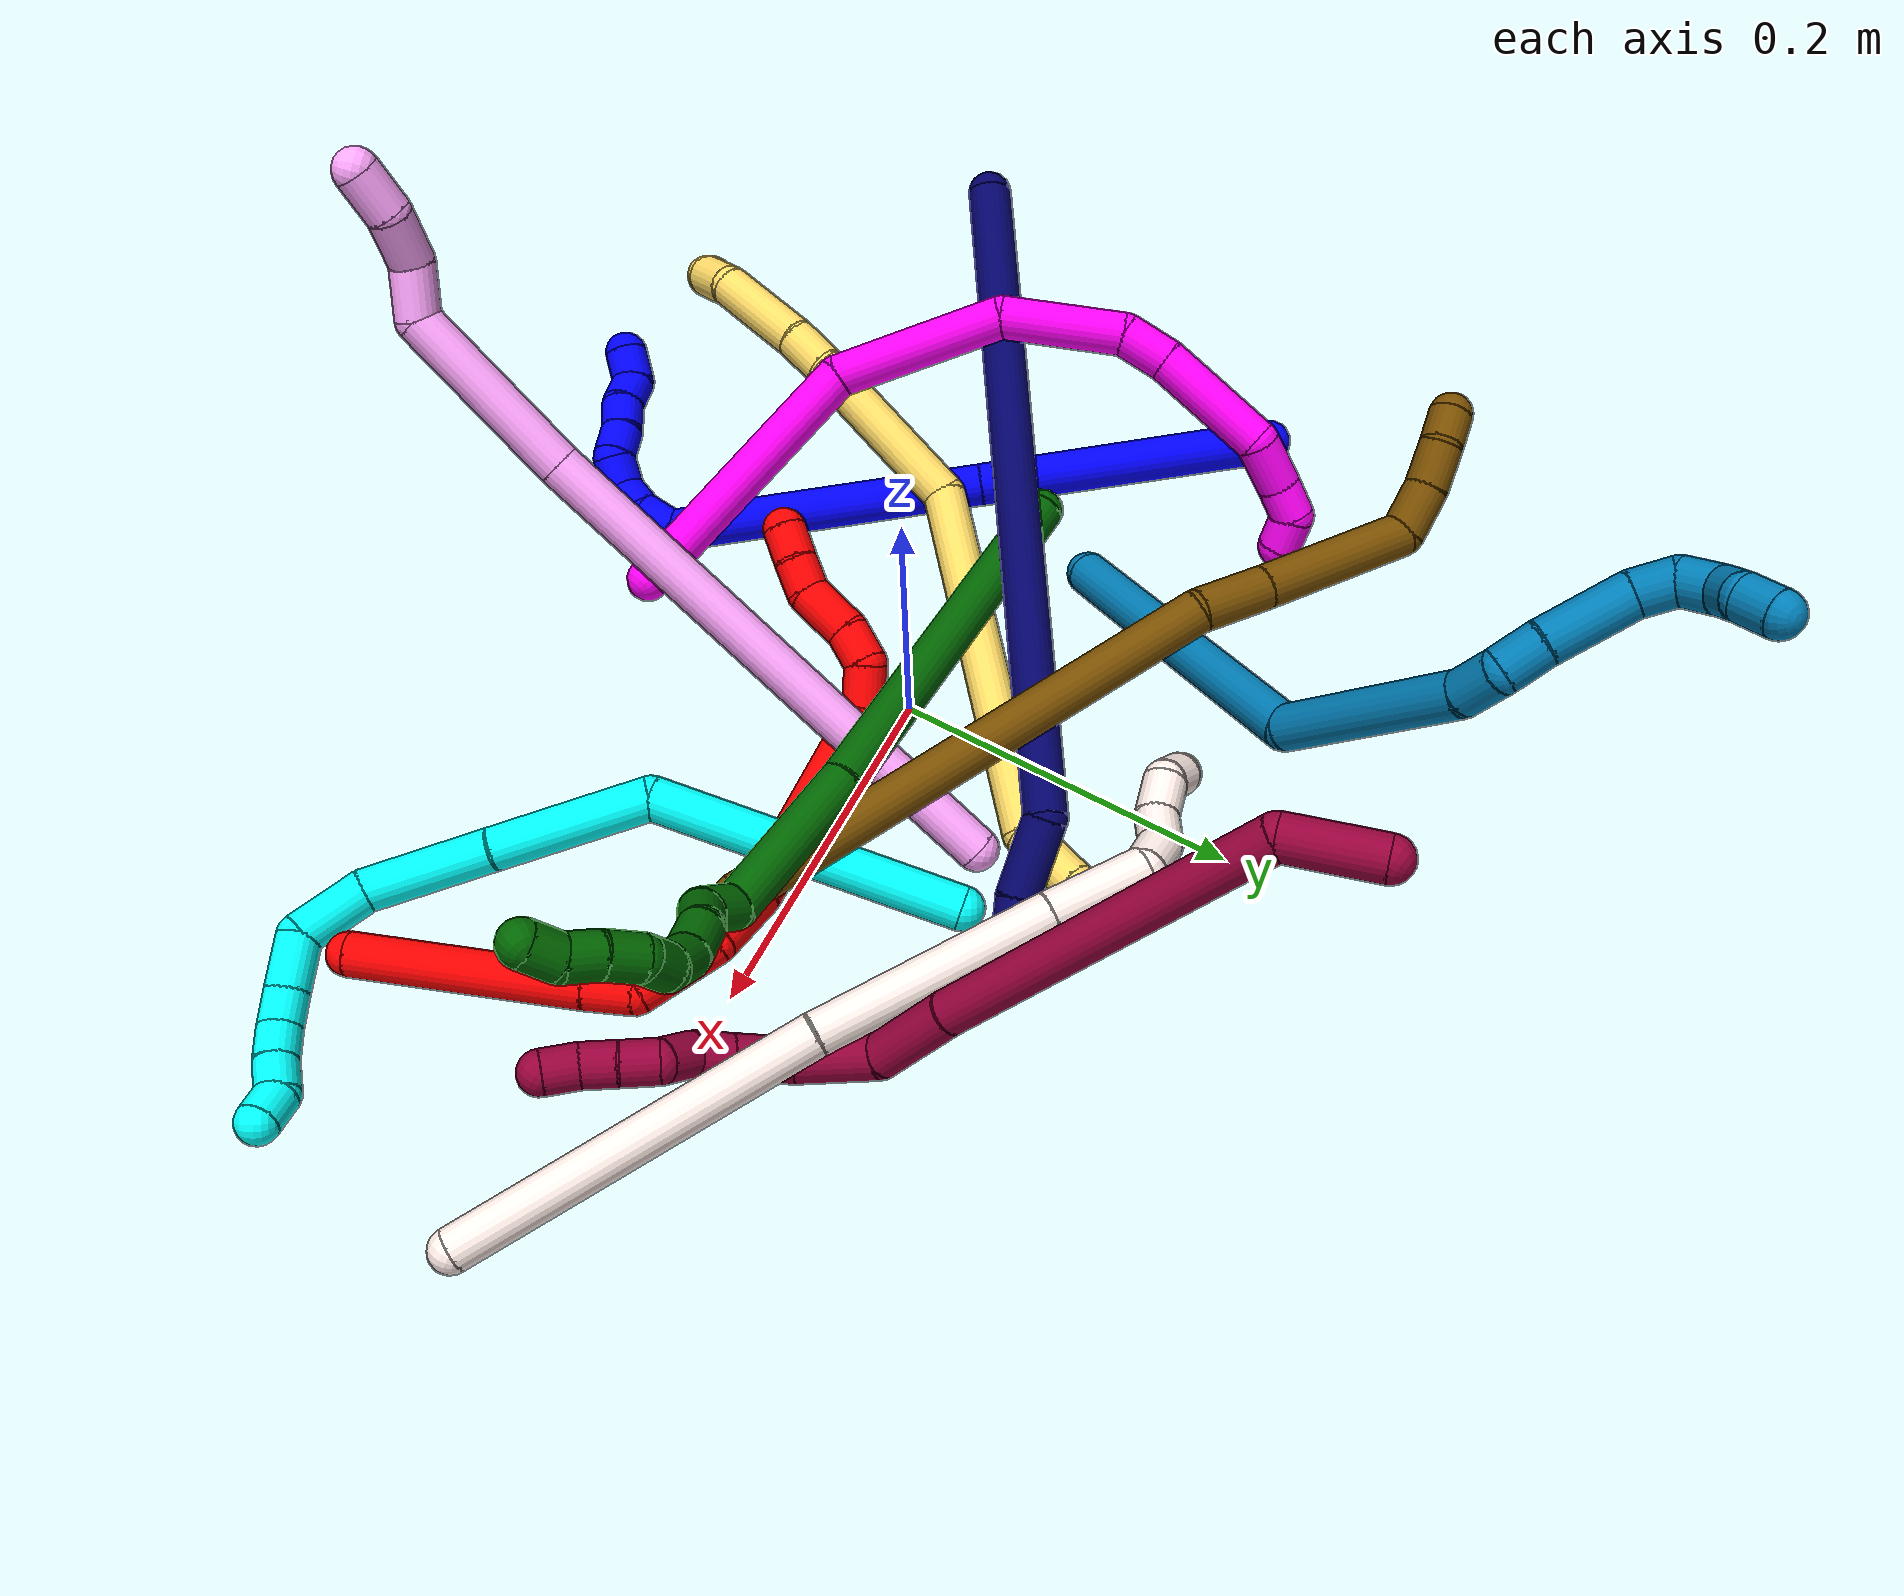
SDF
<sdf version="1.7">
 <world name="default">
  <plugin name="TubeGeneratorPlugin" filename="libtube_generator_plugin.so"/>
  <model name="photoneo_s_sensor">
   <static>1</static>
   <pose>0 0 2 1.57079 1.57079 3.14159</pose>
   <link name="link">
    <inertial><mass>0.1</mass></inertial>
    <sensor name="sensor" type="depth">
     <update_rate>30</update_rate>
     <camera>
      <horizontal_fov>1.22</horizontal_fov>
      <image><width>1920</width><height>1200</height><format>B8G8R8</format></image>
      <clip><near>0.1</near><far>4</far></clip>
      <depth_camera><output>points</output></depth_camera>
     </camera>
     <plugin name="camera_plugin" filename="libgazebo_ros_depth_camera.so">
      <baseline>0.2</baseline>
      <alwaysOn>1</alwaysOn>
      <updateRate>0.0</updateRate>
      <cameraName>camera_ir</cameraName>
      <imageTopicName>/camera/color/image_raw</imageTopicName>
      <cameraInfoTopicName>/camera/color/camera_info</cameraInfoTopicName>
      <depthImageTopicName>/camera/depth/image_raw</depthImageTopicName>
      <depthImageCameraInfoTopicName>/camera/depth/camera_info</depthImageCameraInfoTopicName>
      <pointCloudTopicName>/camera/depth/points</pointCloudTopicName>
      <frameName>fr_optical</frameName>
      <pointCloudCutoff>0.1</pointCloudCutoff>
      <pointCloudCutoffMax>2.0</pointCloudCutoffMax>
      <distortionK1>0</distortionK1>
      <distortionK2>0</distortionK2>
      <distortionK3>0</distortionK3>
      <distortionT1>0</distortionT1>
      <distortionT2>0</distortionT2>
      <CxPrime>0</CxPrime>
      <Cx>0</Cx>
      <Cy>0</Cy>
      <focalLength>0</focalLength>
      <hackBaseline>0</hackBaseline>
     </plugin>
    </sensor>
   </link>
  </model>
  <gravity>0 0 -9.8</gravity>
  <magnetic_field>6e-06 2.3e-05 -4.2e-05</magnetic_field>
  <atmosphere type="adiabatic"/>
  <physics name="default_physics" default="0" type="ode">
   <max_step_size>0.003</max_step_size>
   <real_time_factor>1</real_time_factor>
   <real_time_update_rate>1000</real_time_update_rate>
   <max_contacts>10000</max_contacts>
   <ode>
    <solver>
     <type>quick</type>
     <iters>100</iters>
     <sor>1.3</sor>
     <use_dynamic_moi_rescaling>0</use_dynamic_moi_rescaling>
    </solver>
    <constraints>
     <contact_max_correcting_vel>0</contact_max_correcting_vel>
     <contact_surface_layer>0.001</contact_surface_layer>
     <cfm>0</cfm>
     <erp>0.2</erp>
    </constraints>
   </ode>
  </physics>
  <scene><ambient>0.4 0.4 0.4 1</ambient><background>0.7 0.7 0.7 1</background><shadows>0</shadows></scene>
  <audio><device>default</device></audio>
  <spherical_coordinates>
   <surface_model>EARTH_WGS84</surface_model>
   <latitude_deg>0</latitude_deg>
   <longitude_deg>0</longitude_deg>
   <elevation>0</elevation>
   <heading_deg>0</heading_deg>
  </spherical_coordinates>
  <model name="bin">
   <static>1</static>
   <link name="bottom">
    <collision name="collision-bottom">
     <pose>0 0 -0.01 0 -0 0</pose>
     <geometry><box><size>0.8 0.6 0.02</size></box></geometry>
     <surface>
      <friction><ode><mu>100</mu><mu2>100</mu2></ode></friction>
      <contact><collide_bitmask>65535</collide_bitmask></contact>
     </surface>
    </collision>
   </link>
   <link name="west_wall">
    <collision name="collision-west_wall">
     <pose>-0.41 0 0.1 0 -0 0</pose>
     <geometry><box><size>0.02 0.6 0.2</size></box></geometry>
     <surface>
      <friction><ode><mu>100</mu><mu2>100</mu2></ode></friction>
      <contact><collide_bitmask>65535</collide_bitmask></contact>
     </surface>
    </collision>
   </link>
   <link name="east_wall">
    <collision name="collision-east_wall">
     <pose>0.41 0 0.1 0 -0 0</pose>
     <geometry><box><size>0.02 0.6 0.2</size></box></geometry>
     <surface>
      <friction><ode><mu>100</mu><mu2>100</mu2></ode></friction>
      <contact><collide_bitmask>65535</collide_bitmask></contact>
     </surface>
    </collision>
   </link>
   <link name="south_wall">
    <collision name="collision-south_wall">
     <pose>0 -0.31 0.1 0 -0 0</pose>
     <geometry><box><size>0.8 0.02 0.2</size></box></geometry>
     <surface>
      <friction><ode><mu>100</mu><mu2>100</mu2></ode></friction>
      <contact><collide_bitmask>65535</collide_bitmask></contact>
     </surface>
    </collision>
   </link>
   <link name="north_wall">
    <collision name="collision-north_wall">
     <pose>0 0.31 0.1 0 -0 0</pose>
     <geometry><box><size>0.8 0.02 0.2</size></box></geometry>
     <surface>
      <friction><ode><mu>100</mu><mu2>100</mu2></ode></friction>
      <contact><collide_bitmask>65535</collide_bitmask></contact>
     </surface>
    </collision>
   </link>
  </model>
  <model name="1">
   <static>0</static>
   <link name="1">
    <collision name="collision-cylinder-e_1_1_4">
     <pose>0.017353 -0.06069 0.058128 0.806958 0.203627 0.087175</pose>
     <geometry><cylinder><radius>0.0125</radius><length>0.171618</length></cylinder></geometry>
     <surface>
      <friction><ode><mu>1.16</mu><mu2>1.16</mu2><slip1>0</slip1><slip2>0</slip2></ode></friction>
      <contact><ode><kp>1e+06</kp><kd>1</kd><max_vel>0</max_vel><min_depth>0.001</min_depth></ode></contact>
     </surface>
    </collision>
    <visual name="visual-cylinder-e_1_1_4">
     <pose>0.017353 -0.06069 0.058128 0.806958 0.203627 0.087175</pose>
     <geometry><cylinder><radius>0.0125</radius><length>0.171618</length></cylinder></geometry>
     <material><ambient>0 0 1 1</ambient></material>
    </visual>
    <collision name="collision-cylinder-e_2_4_5">
     <pose>0.072758 -0.169143 0.18653 0.596951 0.421055 0.131304</pose>
     <geometry><cylinder><radius>0.0125</radius><length>0.186204</length></cylinder></geometry>
     <surface>
      <friction><ode><mu>1.16</mu><mu2>1.16</mu2><slip1>0</slip1><slip2>0</slip2></ode></friction>
      <contact><ode><kp>1e+06</kp><kd>1</kd><max_vel>0</max_vel><min_depth>0.001</min_depth></ode></contact>
     </surface>
    </collision>
    <visual name="visual-cylinder-e_2_4_5">
     <pose>0.072758 -0.169143 0.18653 0.596951 0.421055 0.131304</pose>
     <geometry><cylinder><radius>0.0125</radius><length>0.186204</length></cylinder></geometry>
     <material><ambient>0 0 1 1</ambient></material>
    </visual>
    <collision name="collision-cylinder-e_3_5_6">
     <pose>0.107759 -0.220283 0.266455 0.336563 -0.290124 -0.049627</pose>
     <geometry><cylinder><radius>0.0125</radius><length>0.021338</length></cylinder></geometry>
     <surface>
      <friction><ode><mu>1.16</mu><mu2>1.16</mu2><slip1>0</slip1><slip2>0</slip2></ode></friction>
      <contact><ode><kp>1e+06</kp><kd>1</kd><max_vel>0</max_vel><min_depth>0.001</min_depth></ode></contact>
     </surface>
    </collision>
    <visual name="visual-cylinder-e_3_5_6">
     <pose>0.107759 -0.220283 0.266455 0.336563 -0.290124 -0.049627</pose>
     <geometry><cylinder><radius>0.0125</radius><length>0.021338</length></cylinder></geometry>
     <material><ambient>0 0 1 1</ambient></material>
    </visual>
    <collision name="collision-cylinder-e_4_6_7">
     <pose>0.098113 -0.227095 0.283257 0.447834 -0.69337 -0.164182</pose>
     <geometry><cylinder><radius>0.0125</radius><length>0.020633</length></cylinder></geometry>
     <surface>
      <friction><ode><mu>1.16</mu><mu2>1.16</mu2><slip1>0</slip1><slip2>0</slip2></ode></friction>
      <contact><ode><kp>1e+06</kp><kd>1</kd><max_vel>0</max_vel><min_depth>0.001</min_depth></ode></contact>
     </surface>
    </collision>
    <visual name="visual-cylinder-e_4_6_7">
     <pose>0.098113 -0.227095 0.283257 0.447834 -0.69337 -0.164182</pose>
     <geometry><cylinder><radius>0.0125</radius><length>0.020633</length></cylinder></geometry>
     <material><ambient>0 0 1 1</ambient></material>
    </visual>
    <collision name="collision-cylinder-e_5_7_8">
     <pose>0.085151 -0.227593 0.297574 -0.389116 -0.68819 0.140992</pose>
     <geometry><cylinder><radius>0.0125</radius><length>0.020054</length></cylinder></geometry>
     <surface>
      <friction><ode><mu>1.16</mu><mu2>1.16</mu2><slip1>0</slip1><slip2>0</slip2></ode></friction>
      <contact><ode><kp>1e+06</kp><kd>1</kd><max_vel>0</max_vel><min_depth>0.001</min_depth></ode></contact>
     </surface>
    </collision>
    <visual name="visual-cylinder-e_5_7_8">
     <pose>0.085151 -0.227593 0.297574 -0.389116 -0.68819 0.140992</pose>
     <geometry><cylinder><radius>0.0125</radius><length>0.020054</length></cylinder></geometry>
     <material><ambient>0 0 1 1</ambient></material>
    </visual>
    <collision name="collision-cylinder-e_6_8_9">
     <pose>0.068908 -0.223834 0.306217 -0.506913 -1.40137 0.430198</pose>
     <geometry><cylinder><radius>0.0125</radius><length>0.020034</length></cylinder></geometry>
     <surface>
      <friction><ode><mu>1.16</mu><mu2>1.16</mu2><slip1>0</slip1><slip2>0</slip2></ode></friction>
      <contact><ode><kp>1e+06</kp><kd>1</kd><max_vel>0</max_vel><min_depth>0.001</min_depth></ode></contact>
     </surface>
    </collision>
    <visual name="visual-cylinder-e_6_8_9">
     <pose>0.068908 -0.223834 0.306217 -0.506913 -1.40137 0.430198</pose>
     <geometry><cylinder><radius>0.0125</radius><length>0.020034</length></cylinder></geometry>
     <material><ambient>0 0 1 1</ambient></material>
    </visual>
    <collision name="collision-cylinder-e_7_9_10">
     <pose>0.049524 -0.223449 0.310915 0.134048 -1.24147 -0.095918</pose>
     <geometry><cylinder><radius>0.0125</radius><length>0.020103</length></cylinder></geometry>
     <surface>
      <friction><ode><mu>1.16</mu><mu2>1.16</mu2><slip1>0</slip1><slip2>0</slip2></ode></friction>
      <contact><ode><kp>1e+06</kp><kd>1</kd><max_vel>0</max_vel><min_depth>0.001</min_depth></ode></contact>
     </surface>
    </collision>
    <visual name="visual-cylinder-e_7_9_10">
     <pose>0.049524 -0.223449 0.310915 0.134048 -1.24147 -0.095918</pose>
     <geometry><cylinder><radius>0.0125</radius><length>0.020103</length></cylinder></geometry>
     <material><ambient>0 0 1 1</ambient></material>
    </visual>
    <collision name="collision-cylinder-e_8_10_11">
     <pose>0.030017 -0.223597 0.314273 -1.1265 -1.53912 1.09809</pose>
     <geometry><cylinder><radius>0.0125</radius><length>0.020001</length></cylinder></geometry>
     <surface>
      <friction><ode><mu>1.16</mu><mu2>1.16</mu2><slip1>0</slip1><slip2>0</slip2></ode></friction>
      <contact><ode><kp>1e+06</kp><kd>1</kd><max_vel>0</max_vel><min_depth>0.001</min_depth></ode></contact>
     </surface>
    </collision>
    <visual name="visual-cylinder-e_8_10_11">
     <pose>0.030017 -0.223597 0.314273 -1.1265 -1.53912 1.09809</pose>
     <geometry><cylinder><radius>0.0125</radius><length>0.020001</length></cylinder></geometry>
     <material><ambient>0 0 1 1</ambient></material>
    </visual>
    <collision name="collision-cylinder-e_9_11_2">
     <pose>0.012297 -0.221987 0.320632 -0.209664 -0.881837 0.099224</pose>
     <geometry><cylinder><radius>0.0125</radius><length>0.020015</length></cylinder></geometry>
     <surface>
      <friction><ode><mu>1.16</mu><mu2>1.16</mu2><slip1>0</slip1><slip2>0</slip2></ode></friction>
      <contact><ode><kp>1e+06</kp><kd>1</kd><max_vel>0</max_vel><min_depth>0.001</min_depth></ode></contact>
     </surface>
    </collision>
    <visual name="visual-cylinder-e_9_11_2">
     <pose>0.012297 -0.221987 0.320632 -0.209664 -0.881837 0.099224</pose>
     <geometry><cylinder><radius>0.0125</radius><length>0.020015</length></cylinder></geometry>
     <material><ambient>0 0 1 1</ambient></material>
    </visual>
    <collision name="collision-sphere-2">
     <pose>0.004572 -0.220663 0.326855 0 -0 0</pose>
     <geometry><sphere><radius>0.0125</radius></sphere></geometry>
     <surface>
      <friction><ode><mu>1.16</mu><mu2>1.16</mu2><slip1>0</slip1><slip2>0</slip2></ode></friction>
      <contact><ode><kp>1e+06</kp><kd>1</kd><max_vel>0</max_vel><min_depth>0.001</min_depth></ode></contact>
     </surface>
    </collision>
    <visual name="visual-sphere-2">
     <pose>0.004572 -0.220663 0.326855 0 -0 0</pose>
     <geometry><sphere><radius>0.0125</radius></sphere></geometry>
     <material><ambient>0 0 1 1</ambient></material>
    </visual>
    <collision name="collision-sphere-11">
     <pose>0.020022 -0.223311 0.314409 0 -0 0</pose>
     <geometry><sphere><radius>0.0125</radius></sphere></geometry>
     <surface>
      <friction><ode><mu>1.16</mu><mu2>1.16</mu2><slip1>0</slip1><slip2>0</slip2></ode></friction>
      <contact><ode><kp>1e+06</kp><kd>1</kd><max_vel>0</max_vel><min_depth>0.001</min_depth></ode></contact>
     </surface>
    </collision>
    <visual name="visual-sphere-11">
     <pose>0.020022 -0.223311 0.314409 0 -0 0</pose>
     <geometry><sphere><radius>0.0125</radius></sphere></geometry>
     <material><ambient>0 0 1 1</ambient></material>
    </visual>
    <collision name="collision-sphere-10">
     <pose>0.040012 -0.223883 0.314137 0 -0 0</pose>
     <geometry><sphere><radius>0.0125</radius></sphere></geometry>
     <surface>
      <friction><ode><mu>1.16</mu><mu2>1.16</mu2><slip1>0</slip1><slip2>0</slip2></ode></friction>
      <contact><ode><kp>1e+06</kp><kd>1</kd><max_vel>0</max_vel><min_depth>0.001</min_depth></ode></contact>
     </surface>
    </collision>
    <visual name="visual-sphere-10">
     <pose>0.040012 -0.223883 0.314137 0 -0 0</pose>
     <geometry><sphere><radius>0.0125</radius></sphere></geometry>
     <material><ambient>0 0 1 1</ambient></material>
    </visual>
    <collision name="collision-sphere-9">
     <pose>0.059035 -0.223014 0.307694 0 -0 0</pose>
     <geometry><sphere><radius>0.0125</radius></sphere></geometry>
     <surface>
      <friction><ode><mu>1.16</mu><mu2>1.16</mu2><slip1>0</slip1><slip2>0</slip2></ode></friction>
      <contact><ode><kp>1e+06</kp><kd>1</kd><max_vel>0</max_vel><min_depth>0.001</min_depth></ode></contact>
     </surface>
    </collision>
    <visual name="visual-sphere-9">
     <pose>0.059035 -0.223014 0.307694 0 -0 0</pose>
     <geometry><sphere><radius>0.0125</radius></sphere></geometry>
     <material><ambient>0 0 1 1</ambient></material>
    </visual>
    <collision name="collision-sphere-4">
     <pose>0.034705 -0.121379 0.116255 0 -0 0</pose>
     <geometry><sphere><radius>0.0125</radius></sphere></geometry>
     <surface>
      <friction><ode><mu>1.16</mu><mu2>1.16</mu2><slip1>0</slip1><slip2>0</slip2></ode></friction>
      <contact><ode><kp>1e+06</kp><kd>1</kd><max_vel>0</max_vel><min_depth>0.001</min_depth></ode></contact>
     </surface>
    </collision>
    <visual name="visual-sphere-4">
     <pose>0.034705 -0.121379 0.116255 0 -0 0</pose>
     <geometry><sphere><radius>0.0125</radius></sphere></geometry>
     <material><ambient>0 0 1 1</ambient></material>
    </visual>
    <collision name="collision-sphere-1">
     <geometry><sphere><radius>0.0125</radius></sphere></geometry>
     <surface>
      <friction><ode><mu>1.16</mu><mu2>1.16</mu2><slip1>0</slip1><slip2>0</slip2></ode></friction>
      <contact><ode><kp>1e+06</kp><kd>1</kd><max_vel>0</max_vel><min_depth>0.001</min_depth></ode></contact>
     </surface>
    </collision>
    <visual name="visual-sphere-1">
     <geometry><sphere><radius>0.0125</radius></sphere></geometry>
     <material><ambient>0 0 1 1</ambient></material>
    </visual>
    <collision name="collision-sphere-8">
     <pose>0.078782 -0.224654 0.30474 0 -0 0</pose>
     <geometry><sphere><radius>0.0125</radius></sphere></geometry>
     <surface>
      <friction><ode><mu>1.16</mu><mu2>1.16</mu2><slip1>0</slip1><slip2>0</slip2></ode></friction>
      <contact><ode><kp>1e+06</kp><kd>1</kd><max_vel>0</max_vel><min_depth>0.001</min_depth></ode></contact>
     </surface>
    </collision>
    <visual name="visual-sphere-8">
     <pose>0.078782 -0.224654 0.30474 0 -0 0</pose>
     <geometry><sphere><radius>0.0125</radius></sphere></geometry>
     <material><ambient>0 0 1 1</ambient></material>
    </visual>
    <collision name="collision-sphere-5">
     <pose>0.110811 -0.216907 0.256805 0 -0 0</pose>
     <geometry><sphere><radius>0.0125</radius></sphere></geometry>
     <surface>
      <friction><ode><mu>1.16</mu><mu2>1.16</mu2><slip1>0</slip1><slip2>0</slip2></ode></friction>
      <contact><ode><kp>1e+06</kp><kd>1</kd><max_vel>0</max_vel><min_depth>0.001</min_depth></ode></contact>
     </surface>
    </collision>
    <visual name="visual-sphere-5">
     <pose>0.110811 -0.216907 0.256805 0 -0 0</pose>
     <geometry><sphere><radius>0.0125</radius></sphere></geometry>
     <material><ambient>0 0 1 1</ambient></material>
    </visual>
    <collision name="collision-sphere-6">
     <pose>0.104707 -0.223659 0.276104 0 -0 0</pose>
     <geometry><sphere><radius>0.0125</radius></sphere></geometry>
     <surface>
      <friction><ode><mu>1.16</mu><mu2>1.16</mu2><slip1>0</slip1><slip2>0</slip2></ode></friction>
      <contact><ode><kp>1e+06</kp><kd>1</kd><max_vel>0</max_vel><min_depth>0.001</min_depth></ode></contact>
     </surface>
    </collision>
    <visual name="visual-sphere-6">
     <pose>0.104707 -0.223659 0.276104 0 -0 0</pose>
     <geometry><sphere><radius>0.0125</radius></sphere></geometry>
     <material><ambient>0 0 1 1</ambient></material>
    </visual>
    <collision name="collision-sphere-7">
     <pose>0.091519 -0.230531 0.290409 0 -0 0</pose>
     <geometry><sphere><radius>0.0125</radius></sphere></geometry>
     <surface>
      <friction><ode><mu>1.16</mu><mu2>1.16</mu2><slip1>0</slip1><slip2>0</slip2></ode></friction>
      <contact><ode><kp>1e+06</kp><kd>1</kd><max_vel>0</max_vel><min_depth>0.001</min_depth></ode></contact>
     </surface>
    </collision>
    <visual name="visual-sphere-7">
     <pose>0.091519 -0.230531 0.290409 0 -0 0</pose>
     <geometry><sphere><radius>0.0125</radius></sphere></geometry>
     <material><ambient>0 0 1 1</ambient></material>
    </visual>
    <inertial>
     <pose>0.05156 -0.147505 0.174589 0 -0 0</pose>
     <mass>0.5</mass>
     <inertia>
      <ixx>0.001018</ixx>
      <ixy>0</ixy>
      <ixz>0</ixz>
      <iyy>0.000858</iyy>
      <iyz>0</iyz>
      <izz>0.000307</izz>
     </inertia>
    </inertial>
   </link>
   <pose>-0.228629 0.113033 0.053035 1.06771 -0.219204 0.240309</pose>
  </model>
  <model name="2">
   <static>0</static>
   <link name="2">
    <collision name="collision-cylinder-e_1_1_4">
     <pose>-0.022279 0.062234 -0.007847 -1.69622 -0.341283 0.385955</pose>
     <geometry><cylinder><radius>0.0125</radius><length>0.133131</length></cylinder></geometry>
     <surface>
      <friction><ode><mu>1.16</mu><mu2>1.16</mu2><slip1>0</slip1><slip2>0</slip2></ode></friction>
      <contact><ode><kp>1e+06</kp><kd>1</kd><max_vel>0</max_vel><min_depth>0.001</min_depth></ode></contact>
     </surface>
    </collision>
    <visual name="visual-cylinder-e_1_1_4">
     <pose>-0.022279 0.062234 -0.007847 -1.69622 -0.341283 0.385955</pose>
     <geometry><cylinder><radius>0.0125</radius><length>0.133131</length></cylinder></geometry>
     <material><ambient>1 0 0 1</ambient></material>
    </visual>
    <collision name="collision-cylinder-e_2_4_5">
     <pose>-0.049681 0.137267 -0.017551 -1.71484 -0.377097 0.434033</pose>
     <geometry><cylinder><radius>0.0125</radius><length>0.027822</length></cylinder></geometry>
     <surface>
      <friction><ode><mu>1.16</mu><mu2>1.16</mu2><slip1>0</slip1><slip2>0</slip2></ode></friction>
      <contact><ode><kp>1e+06</kp><kd>1</kd><max_vel>0</max_vel><min_depth>0.001</min_depth></ode></contact>
     </surface>
    </collision>
    <visual name="visual-cylinder-e_2_4_5">
     <pose>-0.049681 0.137267 -0.017551 -1.71484 -0.377097 0.434033</pose>
     <geometry><cylinder><radius>0.0125</radius><length>0.027822</length></cylinder></geometry>
     <material><ambient>1 0 0 1</ambient></material>
    </visual>
    <collision name="collision-cylinder-e_3_5_6">
     <pose>-0.072963 0.161054 -0.032307 -2.43611 -0.820016 1.7361</pose>
     <geometry><cylinder><radius>0.0125</radius><length>0.049675</length></cylinder></geometry>
     <surface>
      <friction><ode><mu>1.16</mu><mu2>1.16</mu2><slip1>0</slip1><slip2>0</slip2></ode></friction>
      <contact><ode><kp>1e+06</kp><kd>1</kd><max_vel>0</max_vel><min_depth>0.001</min_depth></ode></contact>
     </surface>
    </collision>
    <visual name="visual-cylinder-e_3_5_6">
     <pose>-0.072963 0.161054 -0.032307 -2.43611 -0.820016 1.7361</pose>
     <geometry><cylinder><radius>0.0125</radius><length>0.049675</length></cylinder></geometry>
     <material><ambient>1 0 0 1</ambient></material>
    </visual>
    <collision name="collision-cylinder-e_4_6_7">
     <pose>-0.101599 0.173568 -0.063053 -3.05622 -0.52922 2.8289</pose>
     <geometry><cylinder><radius>0.0125</radius><length>0.041501</length></cylinder></geometry>
     <surface>
      <friction><ode><mu>1.16</mu><mu2>1.16</mu2><slip1>0</slip1><slip2>0</slip2></ode></friction>
      <contact><ode><kp>1e+06</kp><kd>1</kd><max_vel>0</max_vel><min_depth>0.001</min_depth></ode></contact>
     </surface>
    </collision>
    <visual name="visual-cylinder-e_4_6_7">
     <pose>-0.101599 0.173568 -0.063053 -3.05622 -0.52922 2.8289</pose>
     <geometry><cylinder><radius>0.0125</radius><length>0.041501</length></cylinder></geometry>
     <material><ambient>1 0 0 1</ambient></material>
    </visual>
    <collision name="collision-cylinder-e_5_7_8">
     <pose>-0.160025 0.171353 -0.121111 3.0488 -0.870828 -2.94265</pose>
     <geometry><cylinder><radius>0.0125</radius><length>0.125382</length></cylinder></geometry>
     <surface>
      <friction><ode><mu>1.16</mu><mu2>1.16</mu2><slip1>0</slip1><slip2>0</slip2></ode></friction>
      <contact><ode><kp>1e+06</kp><kd>1</kd><max_vel>0</max_vel><min_depth>0.001</min_depth></ode></contact>
     </surface>
    </collision>
    <visual name="visual-cylinder-e_5_7_8">
     <pose>-0.160025 0.171353 -0.121111 3.0488 -0.870828 -2.94265</pose>
     <geometry><cylinder><radius>0.0125</radius><length>0.125382</length></cylinder></geometry>
     <material><ambient>1 0 0 1</ambient></material>
    </visual>
    <collision name="collision-cylinder-e_6_8_9">
     <pose>-0.220574 0.162343 -0.162456 1.78274 -1.16662 -1.37006</pose>
     <geometry><cylinder><radius>0.0125</radius><length>0.027405</length></cylinder></geometry>
     <surface>
      <friction><ode><mu>1.16</mu><mu2>1.16</mu2><slip1>0</slip1><slip2>0</slip2></ode></friction>
      <contact><ode><kp>1e+06</kp><kd>1</kd><max_vel>0</max_vel><min_depth>0.001</min_depth></ode></contact>
     </surface>
    </collision>
    <visual name="visual-cylinder-e_6_8_9">
     <pose>-0.220574 0.162343 -0.162456 1.78274 -1.16662 -1.37006</pose>
     <geometry><cylinder><radius>0.0125</radius><length>0.027405</length></cylinder></geometry>
     <material><ambient>1 0 0 1</ambient></material>
    </visual>
    <collision name="collision-cylinder-e_7_9_10">
     <pose>-0.238461 0.14765 -0.165975 1.8187 -0.498218 -0.631728</pose>
     <geometry><cylinder><radius>0.0125</radius><length>0.022136</length></cylinder></geometry>
     <surface>
      <friction><ode><mu>1.16</mu><mu2>1.16</mu2><slip1>0</slip1><slip2>0</slip2></ode></friction>
      <contact><ode><kp>1e+06</kp><kd>1</kd><max_vel>0</max_vel><min_depth>0.001</min_depth></ode></contact>
     </surface>
    </collision>
    <visual name="visual-cylinder-e_7_9_10">
     <pose>-0.238461 0.14765 -0.165975 1.8187 -0.498218 -0.631728</pose>
     <geometry><cylinder><radius>0.0125</radius><length>0.022136</length></cylinder></geometry>
     <material><ambient>1 0 0 1</ambient></material>
    </visual>
    <collision name="collision-cylinder-e_8_10_11">
     <pose>-0.247705 0.122737 -0.170501 1.70813 -0.247727 -0.283861</pose>
     <geometry><cylinder><radius>0.0125</radius><length>0.032254</length></cylinder></geometry>
     <surface>
      <friction><ode><mu>1.16</mu><mu2>1.16</mu2><slip1>0</slip1><slip2>0</slip2></ode></friction>
      <contact><ode><kp>1e+06</kp><kd>1</kd><max_vel>0</max_vel><min_depth>0.001</min_depth></ode></contact>
     </surface>
    </collision>
    <visual name="visual-cylinder-e_8_10_11">
     <pose>-0.247705 0.122737 -0.170501 1.70813 -0.247727 -0.283861</pose>
     <geometry><cylinder><radius>0.0125</radius><length>0.032254</length></cylinder></geometry>
     <material><ambient>1 0 0 1</ambient></material>
    </visual>
    <collision name="collision-cylinder-e_9_11_12">
     <pose>-0.257837 0.099521 -0.174525 1.80981 -0.660285 -0.822657</pose>
     <geometry><cylinder><radius>0.0125</radius><length>0.020144</length></cylinder></geometry>
     <surface>
      <friction><ode><mu>1.16</mu><mu2>1.16</mu2><slip1>0</slip1><slip2>0</slip2></ode></friction>
      <contact><ode><kp>1e+06</kp><kd>1</kd><max_vel>0</max_vel><min_depth>0.001</min_depth></ode></contact>
     </surface>
    </collision>
    <visual name="visual-cylinder-e_9_11_12">
     <pose>-0.257837 0.099521 -0.174525 1.80981 -0.660285 -0.822657</pose>
     <geometry><cylinder><radius>0.0125</radius><length>0.020144</length></cylinder></geometry>
     <material><ambient>1 0 0 1</ambient></material>
    </visual>
    <collision name="collision-cylinder-e_10_12_2">
     <pose>-0.270024 0.084045 -0.179482 1.94858 -0.624761 -0.887903</pose>
     <geometry><cylinder><radius>0.0125</radius><length>0.02055</length></cylinder></geometry>
     <surface>
      <friction><ode><mu>1.16</mu><mu2>1.16</mu2><slip1>0</slip1><slip2>0</slip2></ode></friction>
      <contact><ode><kp>1e+06</kp><kd>1</kd><max_vel>0</max_vel><min_depth>0.001</min_depth></ode></contact>
     </surface>
    </collision>
    <visual name="visual-cylinder-e_10_12_2">
     <pose>-0.270024 0.084045 -0.179482 1.94858 -0.624761 -0.887903</pose>
     <geometry><cylinder><radius>0.0125</radius><length>0.02055</length></cylinder></geometry>
     <material><ambient>1 0 0 1</ambient></material>
    </visual>
    <collision name="collision-sphere-2">
     <pose>-0.276034 0.076299 -0.182556 0 -0 0</pose>
     <geometry><sphere><radius>0.0125</radius></sphere></geometry>
     <surface>
      <friction><ode><mu>1.16</mu><mu2>1.16</mu2><slip1>0</slip1><slip2>0</slip2></ode></friction>
      <contact><ode><kp>1e+06</kp><kd>1</kd><max_vel>0</max_vel><min_depth>0.001</min_depth></ode></contact>
     </surface>
    </collision>
    <visual name="visual-sphere-2">
     <pose>-0.276034 0.076299 -0.182556 0 -0 0</pose>
     <geometry><sphere><radius>0.0125</radius></sphere></geometry>
     <material><ambient>1 0 0 1</ambient></material>
    </visual>
    <collision name="collision-sphere-12">
     <pose>-0.264014 0.091792 -0.176408 0 -0 0</pose>
     <geometry><sphere><radius>0.0125</radius></sphere></geometry>
     <surface>
      <friction><ode><mu>1.16</mu><mu2>1.16</mu2><slip1>0</slip1><slip2>0</slip2></ode></friction>
      <contact><ode><kp>1e+06</kp><kd>1</kd><max_vel>0</max_vel><min_depth>0.001</min_depth></ode></contact>
     </surface>
    </collision>
    <visual name="visual-sphere-12">
     <pose>-0.264014 0.091792 -0.176408 0 -0 0</pose>
     <geometry><sphere><radius>0.0125</radius></sphere></geometry>
     <material><ambient>1 0 0 1</ambient></material>
    </visual>
    <collision name="collision-sphere-11">
     <pose>-0.251659 0.10725 -0.172642 0 -0 0</pose>
     <geometry><sphere><radius>0.0125</radius></sphere></geometry>
     <surface>
      <friction><ode><mu>1.16</mu><mu2>1.16</mu2><slip1>0</slip1><slip2>0</slip2></ode></friction>
      <contact><ode><kp>1e+06</kp><kd>1</kd><max_vel>0</max_vel><min_depth>0.001</min_depth></ode></contact>
     </surface>
    </collision>
    <visual name="visual-sphere-11">
     <pose>-0.251659 0.10725 -0.172642 0 -0 0</pose>
     <geometry><sphere><radius>0.0125</radius></sphere></geometry>
     <material><ambient>1 0 0 1</ambient></material>
    </visual>
    <collision name="collision-sphere-10">
     <pose>-0.24375 0.138225 -0.168361 0 -0 0</pose>
     <geometry><sphere><radius>0.0125</radius></sphere></geometry>
     <surface>
      <friction><ode><mu>1.16</mu><mu2>1.16</mu2><slip1>0</slip1><slip2>0</slip2></ode></friction>
      <contact><ode><kp>1e+06</kp><kd>1</kd><max_vel>0</max_vel><min_depth>0.001</min_depth></ode></contact>
     </surface>
    </collision>
    <visual name="visual-sphere-10">
     <pose>-0.24375 0.138225 -0.168361 0 -0 0</pose>
     <geometry><sphere><radius>0.0125</radius></sphere></geometry>
     <material><ambient>1 0 0 1</ambient></material>
    </visual>
    <collision name="collision-sphere-9">
     <pose>-0.233172 0.157075 -0.163589 0 -0 0</pose>
     <geometry><sphere><radius>0.0125</radius></sphere></geometry>
     <surface>
      <friction><ode><mu>1.16</mu><mu2>1.16</mu2><slip1>0</slip1><slip2>0</slip2></ode></friction>
      <contact><ode><kp>1e+06</kp><kd>1</kd><max_vel>0</max_vel><min_depth>0.001</min_depth></ode></contact>
     </surface>
    </collision>
    <visual name="visual-sphere-9">
     <pose>-0.233172 0.157075 -0.163589 0 -0 0</pose>
     <geometry><sphere><radius>0.0125</radius></sphere></geometry>
     <material><ambient>1 0 0 1</ambient></material>
    </visual>
    <collision name="collision-sphere-4">
     <pose>-0.044559 0.124467 -0.015694 0 -0 0</pose>
     <geometry><sphere><radius>0.0125</radius></sphere></geometry>
     <surface>
      <friction><ode><mu>1.16</mu><mu2>1.16</mu2><slip1>0</slip1><slip2>0</slip2></ode></friction>
      <contact><ode><kp>1e+06</kp><kd>1</kd><max_vel>0</max_vel><min_depth>0.001</min_depth></ode></contact>
     </surface>
    </collision>
    <visual name="visual-sphere-4">
     <pose>-0.044559 0.124467 -0.015694 0 -0 0</pose>
     <geometry><sphere><radius>0.0125</radius></sphere></geometry>
     <material><ambient>1 0 0 1</ambient></material>
    </visual>
    <collision name="collision-sphere-1">
     <geometry><sphere><radius>0.0125</radius></sphere></geometry>
     <surface>
      <friction><ode><mu>1.16</mu><mu2>1.16</mu2><slip1>0</slip1><slip2>0</slip2></ode></friction>
      <contact><ode><kp>1e+06</kp><kd>1</kd><max_vel>0</max_vel><min_depth>0.001</min_depth></ode></contact>
     </surface>
    </collision>
    <visual name="visual-sphere-1">
     <geometry><sphere><radius>0.0125</radius></sphere></geometry>
     <material><ambient>1 0 0 1</ambient></material>
    </visual>
    <collision name="collision-sphere-8">
     <pose>-0.207975 0.167611 -0.161322 0 -0 0</pose>
     <geometry><sphere><radius>0.0125</radius></sphere></geometry>
     <surface>
      <friction><ode><mu>1.16</mu><mu2>1.16</mu2><slip1>0</slip1><slip2>0</slip2></ode></friction>
      <contact><ode><kp>1e+06</kp><kd>1</kd><max_vel>0</max_vel><min_depth>0.001</min_depth></ode></contact>
     </surface>
    </collision>
    <visual name="visual-sphere-8">
     <pose>-0.207975 0.167611 -0.161322 0 -0 0</pose>
     <geometry><sphere><radius>0.0125</radius></sphere></geometry>
     <material><ambient>1 0 0 1</ambient></material>
    </visual>
    <collision name="collision-sphere-5">
     <pose>-0.054803 0.150067 -0.019407 0 -0 0</pose>
     <geometry><sphere><radius>0.0125</radius></sphere></geometry>
     <surface>
      <friction><ode><mu>1.16</mu><mu2>1.16</mu2><slip1>0</slip1><slip2>0</slip2></ode></friction>
      <contact><ode><kp>1e+06</kp><kd>1</kd><max_vel>0</max_vel><min_depth>0.001</min_depth></ode></contact>
     </surface>
    </collision>
    <visual name="visual-sphere-5">
     <pose>-0.054803 0.150067 -0.019407 0 -0 0</pose>
     <geometry><sphere><radius>0.0125</radius></sphere></geometry>
     <material><ambient>1 0 0 1</ambient></material>
    </visual>
    <collision name="collision-sphere-6">
     <pose>-0.091123 0.17204 -0.045206 0 -0 0</pose>
     <geometry><sphere><radius>0.0125</radius></sphere></geometry>
     <surface>
      <friction><ode><mu>1.16</mu><mu2>1.16</mu2><slip1>0</slip1><slip2>0</slip2></ode></friction>
      <contact><ode><kp>1e+06</kp><kd>1</kd><max_vel>0</max_vel><min_depth>0.001</min_depth></ode></contact>
     </surface>
    </collision>
    <visual name="visual-sphere-6">
     <pose>-0.091123 0.17204 -0.045206 0 -0 0</pose>
     <geometry><sphere><radius>0.0125</radius></sphere></geometry>
     <material><ambient>1 0 0 1</ambient></material>
    </visual>
    <collision name="collision-sphere-7">
     <pose>-0.112075 0.175095 -0.080899 0 -0 0</pose>
     <geometry><sphere><radius>0.0125</radius></sphere></geometry>
     <surface>
      <friction><ode><mu>1.16</mu><mu2>1.16</mu2><slip1>0</slip1><slip2>0</slip2></ode></friction>
      <contact><ode><kp>1e+06</kp><kd>1</kd><max_vel>0</max_vel><min_depth>0.001</min_depth></ode></contact>
     </surface>
    </collision>
    <visual name="visual-sphere-7">
     <pose>-0.112075 0.175095 -0.080899 0 -0 0</pose>
     <geometry><sphere><radius>0.0125</radius></sphere></geometry>
     <material><ambient>1 0 0 1</ambient></material>
    </visual>
    <inertial>
     <pose>-0.124618 0.128401 -0.083538 0 -0 0</pose>
     <mass>0.5</mass>
     <inertia>
      <ixx>0.000106</ixx>
      <ixy>0</ixy>
      <ixz>0</ixz>
      <iyy>0.000249</iyy>
      <iyz>0</iyz>
      <izz>2.4e-05</izz>
     </inertia>
    </inertial>
   </link>
   <pose>0.279298 -0.191994 0.012345 -0.077046 0.692833 -0.066193</pose>
  </model>
  <model name="3">
   <static>0</static>
   <link name="3">
    <collision name="collision-cylinder-e_1_1_4">
     <pose>-0.008405 -0.033027 0.082955 0.378891 -0.093858 -0.01801</pose>
     <geometry><cylinder><radius>0.0125</radius><length>0.179365</length></cylinder></geometry>
     <surface>
      <friction><ode><mu>1.16</mu><mu2>1.16</mu2><slip1>0</slip1><slip2>0</slip2></ode></friction>
      <contact><ode><kp>1e+06</kp><kd>1</kd><max_vel>0</max_vel><min_depth>0.001</min_depth></ode></contact>
     </surface>
    </collision>
    <visual name="visual-cylinder-e_1_1_4">
     <pose>-0.008405 -0.033027 0.082955 0.378891 -0.093858 -0.01801</pose>
     <geometry><cylinder><radius>0.0125</radius><length>0.179365</length></cylinder></geometry>
     <material><ambient>0.003922 1 0.996078 1</ambient></material>
    </visual>
    <collision name="collision-cylinder-e_2_4_5">
     <pose>-0.005443 -0.058285 0.209159 -0.177715 0.253142 -0.022673</pose>
     <geometry><cylinder><radius>0.0125</radius><length>0.090776</length></cylinder></geometry>
     <surface>
      <friction><ode><mu>1.16</mu><mu2>1.16</mu2><slip1>0</slip1><slip2>0</slip2></ode></friction>
      <contact><ode><kp>1e+06</kp><kd>1</kd><max_vel>0</max_vel><min_depth>0.001</min_depth></ode></contact>
     </surface>
    </collision>
    <visual name="visual-cylinder-e_2_4_5">
     <pose>-0.005443 -0.058285 0.209159 -0.177715 0.253142 -0.022673</pose>
     <geometry><cylinder><radius>0.0125</radius><length>0.090776</length></cylinder></geometry>
     <material><ambient>0.003922 1 0.996078 1</ambient></material>
    </visual>
    <collision name="collision-cylinder-e_3_5_6">
     <pose>0.018727 -0.046612 0.287706 -0.110202 0.346017 -0.019277</pose>
     <geometry><cylinder><radius>0.0125</radius><length>0.0755</length></cylinder></geometry>
     <surface>
      <friction><ode><mu>1.16</mu><mu2>1.16</mu2><slip1>0</slip1><slip2>0</slip2></ode></friction>
      <contact><ode><kp>1e+06</kp><kd>1</kd><max_vel>0</max_vel><min_depth>0.001</min_depth></ode></contact>
     </surface>
    </collision>
    <visual name="visual-cylinder-e_3_5_6">
     <pose>0.018727 -0.046612 0.287706 -0.110202 0.346017 -0.019277</pose>
     <geometry><cylinder><radius>0.0125</radius><length>0.0755</length></cylinder></geometry>
     <material><ambient>0.003922 1 0.996078 1</ambient></material>
    </visual>
    <collision name="collision-cylinder-e_4_6_7">
     <pose>0.032409 -0.029456 0.339735 -0.669791 0.041139 -0.014318</pose>
     <geometry><cylinder><radius>0.0125</radius><length>0.042723</length></cylinder></geometry>
     <surface>
      <friction><ode><mu>1.16</mu><mu2>1.16</mu2><slip1>0</slip1><slip2>0</slip2></ode></friction>
      <contact><ode><kp>1e+06</kp><kd>1</kd><max_vel>0</max_vel><min_depth>0.001</min_depth></ode></contact>
     </surface>
    </collision>
    <visual name="visual-cylinder-e_4_6_7">
     <pose>0.032409 -0.029456 0.339735 -0.669791 0.041139 -0.014318</pose>
     <geometry><cylinder><radius>0.0125</radius><length>0.042723</length></cylinder></geometry>
     <material><ambient>0.003922 1 0.996078 1</ambient></material>
    </visual>
    <collision name="collision-cylinder-e_5_7_8">
     <pose>0.038143 -0.001668 0.359189 -1.38569 0.317214 -0.264016</pose>
     <geometry><cylinder><radius>0.0125</radius><length>0.031132</length></cylinder></geometry>
     <surface>
      <friction><ode><mu>1.16</mu><mu2>1.16</mu2><slip1>0</slip1><slip2>0</slip2></ode></friction>
      <contact><ode><kp>1e+06</kp><kd>1</kd><max_vel>0</max_vel><min_depth>0.001</min_depth></ode></contact>
     </surface>
    </collision>
    <visual name="visual-cylinder-e_5_7_8">
     <pose>0.038143 -0.001668 0.359189 -1.38569 0.317214 -0.264016</pose>
     <geometry><cylinder><radius>0.0125</radius><length>0.031132</length></cylinder></geometry>
     <material><ambient>0.003922 1 0.996078 1</ambient></material>
    </visual>
    <collision name="collision-cylinder-e_6_8_9">
     <pose>0.045518 0.022497 0.363334 -1.42405 0.253309 -0.218918</pose>
     <geometry><cylinder><radius>0.0125</radius><length>0.020108</length></cylinder></geometry>
     <surface>
      <friction><ode><mu>1.16</mu><mu2>1.16</mu2><slip1>0</slip1><slip2>0</slip2></ode></friction>
      <contact><ode><kp>1e+06</kp><kd>1</kd><max_vel>0</max_vel><min_depth>0.001</min_depth></ode></contact>
     </surface>
    </collision>
    <visual name="visual-cylinder-e_6_8_9">
     <pose>0.045518 0.022497 0.363334 -1.42405 0.253309 -0.218918</pose>
     <geometry><cylinder><radius>0.0125</radius><length>0.020108</length></cylinder></geometry>
     <material><ambient>0.003922 1 0.996078 1</ambient></material>
    </visual>
    <collision name="collision-cylinder-e_7_9_10">
     <pose>0.048113 0.042248 0.364919 -1.55485 0.007499 -0.00738</pose>
     <geometry><cylinder><radius>0.0125</radius><length>0.020248</length></cylinder></geometry>
     <surface>
      <friction><ode><mu>1.16</mu><mu2>1.16</mu2><slip1>0</slip1><slip2>0</slip2></ode></friction>
      <contact><ode><kp>1e+06</kp><kd>1</kd><max_vel>0</max_vel><min_depth>0.001</min_depth></ode></contact>
     </surface>
    </collision>
    <visual name="visual-cylinder-e_7_9_10">
     <pose>0.048113 0.042248 0.364919 -1.55485 0.007499 -0.00738</pose>
     <geometry><cylinder><radius>0.0125</radius><length>0.020248</length></cylinder></geometry>
     <material><ambient>0.003922 1 0.996078 1</ambient></material>
    </visual>
    <collision name="collision-cylinder-e_8_10_11">
     <pose>0.048024 0.062316 0.363615 -1.71709 -0.016406 0.019</pose>
     <geometry><cylinder><radius>0.0125</radius><length>0.020108</length></cylinder></geometry>
     <surface>
      <friction><ode><mu>1.16</mu><mu2>1.16</mu2><slip1>0</slip1><slip2>0</slip2></ode></friction>
      <contact><ode><kp>1e+06</kp><kd>1</kd><max_vel>0</max_vel><min_depth>0.001</min_depth></ode></contact>
     </surface>
    </collision>
    <visual name="visual-cylinder-e_8_10_11">
     <pose>0.048024 0.062316 0.363615 -1.71709 -0.016406 0.019</pose>
     <geometry><cylinder><radius>0.0125</radius><length>0.020108</length></cylinder></geometry>
     <material><ambient>0.003922 1 0.996078 1</ambient></material>
    </visual>
    <collision name="collision-cylinder-e_9_11_2">
     <pose>0.045648 0.081193 0.366115 -1.15295 -0.222561 0.145041</pose>
     <geometry><cylinder><radius>0.0125</radius><length>0.020041</length></cylinder></geometry>
     <surface>
      <friction><ode><mu>1.16</mu><mu2>1.16</mu2><slip1>0</slip1><slip2>0</slip2></ode></friction>
      <contact><ode><kp>1e+06</kp><kd>1</kd><max_vel>0</max_vel><min_depth>0.001</min_depth></ode></contact>
     </surface>
    </collision>
    <visual name="visual-cylinder-e_9_11_2">
     <pose>0.045648 0.081193 0.366115 -1.15295 -0.222561 0.145041</pose>
     <geometry><cylinder><radius>0.0125</radius><length>0.020041</length></cylinder></geometry>
     <material><ambient>0.003922 1 0.996078 1</ambient></material>
    </visual>
    <collision name="collision-sphere-2">
     <pose>0.043436 0.090126 0.370081 0 -0 0</pose>
     <geometry><sphere><radius>0.0125</radius></sphere></geometry>
     <surface>
      <friction><ode><mu>1.16</mu><mu2>1.16</mu2><slip1>0</slip1><slip2>0</slip2></ode></friction>
      <contact><ode><kp>1e+06</kp><kd>1</kd><max_vel>0</max_vel><min_depth>0.001</min_depth></ode></contact>
     </surface>
    </collision>
    <visual name="visual-sphere-2">
     <pose>0.043436 0.090126 0.370081 0 -0 0</pose>
     <geometry><sphere><radius>0.0125</radius></sphere></geometry>
     <material><ambient>0.003922 1 0.996078 1</ambient></material>
    </visual>
    <collision name="collision-sphere-11">
     <pose>0.047859 0.072261 0.362149 0 -0 0</pose>
     <geometry><sphere><radius>0.0125</radius></sphere></geometry>
     <surface>
      <friction><ode><mu>1.16</mu><mu2>1.16</mu2><slip1>0</slip1><slip2>0</slip2></ode></friction>
      <contact><ode><kp>1e+06</kp><kd>1</kd><max_vel>0</max_vel><min_depth>0.001</min_depth></ode></contact>
     </surface>
    </collision>
    <visual name="visual-sphere-11">
     <pose>0.047859 0.072261 0.362149 0 -0 0</pose>
     <geometry><sphere><radius>0.0125</radius></sphere></geometry>
     <material><ambient>0.003922 1 0.996078 1</ambient></material>
    </visual>
    <collision name="collision-sphere-10">
     <pose>0.048189 0.052371 0.36508 0 -0 0</pose>
     <geometry><sphere><radius>0.0125</radius></sphere></geometry>
     <surface>
      <friction><ode><mu>1.16</mu><mu2>1.16</mu2><slip1>0</slip1><slip2>0</slip2></ode></friction>
      <contact><ode><kp>1e+06</kp><kd>1</kd><max_vel>0</max_vel><min_depth>0.001</min_depth></ode></contact>
     </surface>
    </collision>
    <visual name="visual-sphere-10">
     <pose>0.048189 0.052371 0.36508 0 -0 0</pose>
     <geometry><sphere><radius>0.0125</radius></sphere></geometry>
     <material><ambient>0.003922 1 0.996078 1</ambient></material>
    </visual>
    <collision name="collision-sphere-9">
     <pose>0.048037 0.032125 0.364757 0 -0 0</pose>
     <geometry><sphere><radius>0.0125</radius></sphere></geometry>
     <surface>
      <friction><ode><mu>1.16</mu><mu2>1.16</mu2><slip1>0</slip1><slip2>0</slip2></ode></friction>
      <contact><ode><kp>1e+06</kp><kd>1</kd><max_vel>0</max_vel><min_depth>0.001</min_depth></ode></contact>
     </surface>
    </collision>
    <visual name="visual-sphere-9">
     <pose>0.048037 0.032125 0.364757 0 -0 0</pose>
     <geometry><sphere><radius>0.0125</radius></sphere></geometry>
     <material><ambient>0.003922 1 0.996078 1</ambient></material>
    </visual>
    <collision name="collision-sphere-4">
     <pose>-0.01681 -0.066053 0.16591 0 -0 0</pose>
     <geometry><sphere><radius>0.0125</radius></sphere></geometry>
     <surface>
      <friction><ode><mu>1.16</mu><mu2>1.16</mu2><slip1>0</slip1><slip2>0</slip2></ode></friction>
      <contact><ode><kp>1e+06</kp><kd>1</kd><max_vel>0</max_vel><min_depth>0.001</min_depth></ode></contact>
     </surface>
    </collision>
    <visual name="visual-sphere-4">
     <pose>-0.01681 -0.066053 0.16591 0 -0 0</pose>
     <geometry><sphere><radius>0.0125</radius></sphere></geometry>
     <material><ambient>0.003922 1 0.996078 1</ambient></material>
    </visual>
    <collision name="collision-sphere-1">
     <geometry><sphere><radius>0.0125</radius></sphere></geometry>
     <surface>
      <friction><ode><mu>1.16</mu><mu2>1.16</mu2><slip1>0</slip1><slip2>0</slip2></ode></friction>
      <contact><ode><kp>1e+06</kp><kd>1</kd><max_vel>0</max_vel><min_depth>0.001</min_depth></ode></contact>
     </surface>
    </collision>
    <visual name="visual-sphere-1">
     <geometry><sphere><radius>0.0125</radius></sphere></geometry>
     <material><ambient>0.003922 1 0.996078 1</ambient></material>
    </visual>
    <collision name="collision-sphere-8">
     <pose>0.042998 0.012869 0.361911 0 -0 0</pose>
     <geometry><sphere><radius>0.0125</radius></sphere></geometry>
     <surface>
      <friction><ode><mu>1.16</mu><mu2>1.16</mu2><slip1>0</slip1><slip2>0</slip2></ode></friction>
      <contact><ode><kp>1e+06</kp><kd>1</kd><max_vel>0</max_vel><min_depth>0.001</min_depth></ode></contact>
     </surface>
    </collision>
    <visual name="visual-sphere-8">
     <pose>0.042998 0.012869 0.361911 0 -0 0</pose>
     <geometry><sphere><radius>0.0125</radius></sphere></geometry>
     <material><ambient>0.003922 1 0.996078 1</ambient></material>
    </visual>
    <collision name="collision-sphere-5">
     <pose>0.005924 -0.050517 0.252408 0 -0 0</pose>
     <geometry><sphere><radius>0.0125</radius></sphere></geometry>
     <surface>
      <friction><ode><mu>1.16</mu><mu2>1.16</mu2><slip1>0</slip1><slip2>0</slip2></ode></friction>
      <contact><ode><kp>1e+06</kp><kd>1</kd><max_vel>0</max_vel><min_depth>0.001</min_depth></ode></contact>
     </surface>
    </collision>
    <visual name="visual-sphere-5">
     <pose>0.005924 -0.050517 0.252408 0 -0 0</pose>
     <geometry><sphere><radius>0.0125</radius></sphere></geometry>
     <material><ambient>0.003922 1 0.996078 1</ambient></material>
    </visual>
    <collision name="collision-sphere-6">
     <pose>0.03153 -0.042706 0.323003 0 -0 0</pose>
     <geometry><sphere><radius>0.0125</radius></sphere></geometry>
     <surface>
      <friction><ode><mu>1.16</mu><mu2>1.16</mu2><slip1>0</slip1><slip2>0</slip2></ode></friction>
      <contact><ode><kp>1e+06</kp><kd>1</kd><max_vel>0</max_vel><min_depth>0.001</min_depth></ode></contact>
     </surface>
    </collision>
    <visual name="visual-sphere-6">
     <pose>0.03153 -0.042706 0.323003 0 -0 0</pose>
     <geometry><sphere><radius>0.0125</radius></sphere></geometry>
     <material><ambient>0.003922 1 0.996078 1</ambient></material>
    </visual>
    <collision name="collision-sphere-7">
     <pose>0.033287 -0.016205 0.356467 0 -0 0</pose>
     <geometry><sphere><radius>0.0125</radius></sphere></geometry>
     <surface>
      <friction><ode><mu>1.16</mu><mu2>1.16</mu2><slip1>0</slip1><slip2>0</slip2></ode></friction>
      <contact><ode><kp>1e+06</kp><kd>1</kd><max_vel>0</max_vel><min_depth>0.001</min_depth></ode></contact>
     </surface>
    </collision>
    <visual name="visual-sphere-7">
     <pose>0.033287 -0.016205 0.356467 0 -0 0</pose>
     <geometry><sphere><radius>0.0125</radius></sphere></geometry>
     <material><ambient>0.003922 1 0.996078 1</ambient></material>
    </visual>
    <inertial>
     <pose>0.011509 -0.023712 0.221256 0 -0 0</pose>
     <mass>0.5</mass>
     <inertia>
      <ixx>0.000595</ixx>
      <ixy>0</ixy>
      <ixz>0</ixz>
      <iyy>0.00056</iyy>
      <iyz>0</iyz>
      <izz>0.000194</izz>
     </inertia>
    </inertial>
   </link>
   <pose>0.102957 0.089627 0.024455 1.12674 1.38009 0.122555</pose>
  </model>
  <model name="4">
   <static>0</static>
   <link name="4">
    <collision name="collision-cylinder-e_1_1_4">
     <pose>-0.013681 -0.074809 0.133841 0.509679 -0.08899 -0.023197</pose>
     <geometry><cylinder><radius>0.0125</radius><length>0.307876</length></cylinder></geometry>
     <surface>
      <friction><ode><mu>1.16</mu><mu2>1.16</mu2><slip1>0</slip1><slip2>0</slip2></ode></friction>
      <contact><ode><kp>1e+06</kp><kd>1</kd><max_vel>0</max_vel><min_depth>0.001</min_depth></ode></contact>
     </surface>
    </collision>
    <visual name="visual-cylinder-e_1_1_4">
     <pose>-0.013681 -0.074809 0.133841 0.509679 -0.08899 -0.023197</pose>
     <geometry><cylinder><radius>0.0125</radius><length>0.307876</length></cylinder></geometry>
     <material><ambient>1 0.65098 0.996078 1</ambient></material>
    </visual>
    <collision name="collision-cylinder-e_2_4_5">
     <pose>-0.034555 -0.177008 0.311288 0.560847 -0.138789 -0.040032</pose>
     <geometry><cylinder><radius>0.0125</radius><length>0.103988</length></cylinder></geometry>
     <surface>
      <friction><ode><mu>1.16</mu><mu2>1.16</mu2><slip1>0</slip1><slip2>0</slip2></ode></friction>
      <contact><ode><kp>1e+06</kp><kd>1</kd><max_vel>0</max_vel><min_depth>0.001</min_depth></ode></contact>
     </surface>
    </collision>
    <visual name="visual-cylinder-e_2_4_5">
     <pose>-0.034555 -0.177008 0.311288 0.560847 -0.138789 -0.040032</pose>
     <geometry><cylinder><radius>0.0125</radius><length>0.103988</length></cylinder></geometry>
     <material><ambient>1 0.65098 0.996078 1</ambient></material>
    </visual>
    <collision name="collision-cylinder-e_3_5_6">
     <pose>-0.046474 -0.218095 0.359371 1.25483 -0.316919 -0.230733</pose>
     <geometry><cylinder><radius>0.0125</radius><length>0.030332</length></cylinder></geometry>
     <surface>
      <friction><ode><mu>1.16</mu><mu2>1.16</mu2><slip1>0</slip1><slip2>0</slip2></ode></friction>
      <contact><ode><kp>1e+06</kp><kd>1</kd><max_vel>0</max_vel><min_depth>0.001</min_depth></ode></contact>
     </surface>
    </collision>
    <visual name="visual-cylinder-e_3_5_6">
     <pose>-0.046474 -0.218095 0.359371 1.25483 -0.316919 -0.230733</pose>
     <geometry><cylinder><radius>0.0125</radius><length>0.030332</length></cylinder></geometry>
     <material><ambient>1 0.65098 0.996078 1</ambient></material>
    </visual>
    <collision name="collision-cylinder-e_4_6_7">
     <pose>-0.062109 -0.240329 0.370729 0.892491 -0.782851 -0.389904</pose>
     <geometry><cylinder><radius>0.0125</radius><length>0.030932</length></cylinder></geometry>
     <surface>
      <friction><ode><mu>1.16</mu><mu2>1.16</mu2><slip1>0</slip1><slip2>0</slip2></ode></friction>
      <contact><ode><kp>1e+06</kp><kd>1</kd><max_vel>0</max_vel><min_depth>0.001</min_depth></ode></contact>
     </surface>
    </collision>
    <visual name="visual-cylinder-e_4_6_7">
     <pose>-0.062109 -0.240329 0.370729 0.892491 -0.782851 -0.389904</pose>
     <geometry><cylinder><radius>0.0125</radius><length>0.030932</length></cylinder></geometry>
     <material><ambient>1 0.65098 0.996078 1</ambient></material>
    </visual>
    <collision name="collision-cylinder-e_5_7_2">
     <pose>-0.079396 -0.256109 0.386956 0.659196 -0.494692 -0.172332</pose>
     <geometry><cylinder><radius>0.0125</radius><length>0.026871</length></cylinder></geometry>
     <surface>
      <friction><ode><mu>1.16</mu><mu2>1.16</mu2><slip1>0</slip1><slip2>0</slip2></ode></friction>
      <contact><ode><kp>1e+06</kp><kd>1</kd><max_vel>0</max_vel><min_depth>0.001</min_depth></ode></contact>
     </surface>
    </collision>
    <visual name="visual-cylinder-e_5_7_2">
     <pose>-0.079396 -0.256109 0.386956 0.659196 -0.494692 -0.172332</pose>
     <geometry><cylinder><radius>0.0125</radius><length>0.026871</length></cylinder></geometry>
     <material><ambient>1 0.65098 0.996078 1</ambient></material>
    </visual>
    <collision name="collision-sphere-2">
     <pose>-0.085775 -0.263351 0.396303 0 -0 0</pose>
     <geometry><sphere><radius>0.0125</radius></sphere></geometry>
     <surface>
      <friction><ode><mu>1.16</mu><mu2>1.16</mu2><slip1>0</slip1><slip2>0</slip2></ode></friction>
      <contact><ode><kp>1e+06</kp><kd>1</kd><max_vel>0</max_vel><min_depth>0.001</min_depth></ode></contact>
     </surface>
    </collision>
    <visual name="visual-sphere-2">
     <pose>-0.085775 -0.263351 0.396303 0 -0 0</pose>
     <geometry><sphere><radius>0.0125</radius></sphere></geometry>
     <material><ambient>1 0.65098 0.996078 1</ambient></material>
    </visual>
    <collision name="collision-sphere-7">
     <pose>-0.073017 -0.248866 0.377608 0 -0 0</pose>
     <geometry><sphere><radius>0.0125</radius></sphere></geometry>
     <surface>
      <friction><ode><mu>1.16</mu><mu2>1.16</mu2><slip1>0</slip1><slip2>0</slip2></ode></friction>
      <contact><ode><kp>1e+06</kp><kd>1</kd><max_vel>0</max_vel><min_depth>0.001</min_depth></ode></contact>
     </surface>
    </collision>
    <visual name="visual-sphere-7">
     <pose>-0.073017 -0.248866 0.377608 0 -0 0</pose>
     <geometry><sphere><radius>0.0125</radius></sphere></geometry>
     <material><ambient>1 0.65098 0.996078 1</ambient></material>
    </visual>
    <collision name="collision-sphere-6">
     <pose>-0.051201 -0.231792 0.363849 0 -0 0</pose>
     <geometry><sphere><radius>0.0125</radius></sphere></geometry>
     <surface>
      <friction><ode><mu>1.16</mu><mu2>1.16</mu2><slip1>0</slip1><slip2>0</slip2></ode></friction>
      <contact><ode><kp>1e+06</kp><kd>1</kd><max_vel>0</max_vel><min_depth>0.001</min_depth></ode></contact>
     </surface>
    </collision>
    <visual name="visual-sphere-6">
     <pose>-0.051201 -0.231792 0.363849 0 -0 0</pose>
     <geometry><sphere><radius>0.0125</radius></sphere></geometry>
     <material><ambient>1 0.65098 0.996078 1</ambient></material>
    </visual>
    <collision name="collision-sphere-5">
     <pose>-0.041748 -0.204398 0.354893 0 -0 0</pose>
     <geometry><sphere><radius>0.0125</radius></sphere></geometry>
     <surface>
      <friction><ode><mu>1.16</mu><mu2>1.16</mu2><slip1>0</slip1><slip2>0</slip2></ode></friction>
      <contact><ode><kp>1e+06</kp><kd>1</kd><max_vel>0</max_vel><min_depth>0.001</min_depth></ode></contact>
     </surface>
    </collision>
    <visual name="visual-sphere-5">
     <pose>-0.041748 -0.204398 0.354893 0 -0 0</pose>
     <geometry><sphere><radius>0.0125</radius></sphere></geometry>
     <material><ambient>1 0.65098 0.996078 1</ambient></material>
    </visual>
    <collision name="collision-sphere-1">
     <geometry><sphere><radius>0.0125</radius></sphere></geometry>
     <surface>
      <friction><ode><mu>1.16</mu><mu2>1.16</mu2><slip1>0</slip1><slip2>0</slip2></ode></friction>
      <contact><ode><kp>1e+06</kp><kd>1</kd><max_vel>0</max_vel><min_depth>0.001</min_depth></ode></contact>
     </surface>
    </collision>
    <visual name="visual-sphere-1">
     <geometry><sphere><radius>0.0125</radius></sphere></geometry>
     <material><ambient>1 0.65098 0.996078 1</ambient></material>
    </visual>
    <collision name="collision-sphere-4">
     <pose>-0.027362 -0.149618 0.267682 0 -0 0</pose>
     <geometry><sphere><radius>0.0125</radius></sphere></geometry>
     <surface>
      <friction><ode><mu>1.16</mu><mu2>1.16</mu2><slip1>0</slip1><slip2>0</slip2></ode></friction>
      <contact><ode><kp>1e+06</kp><kd>1</kd><max_vel>0</max_vel><min_depth>0.001</min_depth></ode></contact>
     </surface>
    </collision>
    <visual name="visual-sphere-4">
     <pose>-0.027362 -0.149618 0.267682 0 -0 0</pose>
     <geometry><sphere><radius>0.0125</radius></sphere></geometry>
     <material><ambient>1 0.65098 0.996078 1</ambient></material>
    </visual>
    <inertial>
     <pose>-0.026539 -0.124739 0.212685 0 -0 0</pose>
     <mass>0.5</mass>
     <inertia>
      <ixx>0.002469</ixx>
      <ixy>0</ixy>
      <ixz>0</ixz>
      <iyy>0.002142</iyy>
      <iyz>0</iyz>
      <izz>0.001512</izz>
     </inertia>
    </inertial>
   </link>
   <pose>0.063412 0.077308 0.011495 -1.07364 1.12691 -2.34518</pose>
  </model>
  <model name="5">
   <static>0</static>
   <link name="5">
    <collision name="collision-cylinder-e_1_1_4">
     <pose>-0.011448 -0.01633 0.00375 1.34509 -0.599393 -0.482593</pose>
     <geometry><cylinder><radius>0.0125</radius><length>0.040585</length></cylinder></geometry>
     <surface>
      <friction><ode><mu>1.16</mu><mu2>1.16</mu2><slip1>0</slip1><slip2>0</slip2></ode></friction>
      <contact><ode><kp>1e+06</kp><kd>1</kd><max_vel>0</max_vel><min_depth>0.001</min_depth></ode></contact>
     </surface>
    </collision>
    <visual name="visual-cylinder-e_1_1_4">
     <pose>-0.011448 -0.01633 0.00375 1.34509 -0.599393 -0.482593</pose>
     <geometry><cylinder><radius>0.0125</radius><length>0.040585</length></cylinder></geometry>
     <material><ambient>1 0.858824 0.4 1</ambient></material>
    </visual>
    <collision name="collision-cylinder-e_2_4_5">
     <pose>-0.10929 -0.076002 0.05295 0.761659 -0.942216 -0.402353</pose>
     <geometry><cylinder><radius>0.0125</radius><length>0.213618</length></cylinder></geometry>
     <surface>
      <friction><ode><mu>1.16</mu><mu2>1.16</mu2><slip1>0</slip1><slip2>0</slip2></ode></friction>
      <contact><ode><kp>1e+06</kp><kd>1</kd><max_vel>0</max_vel><min_depth>0.001</min_depth></ode></contact>
     </surface>
    </collision>
    <visual name="visual-cylinder-e_2_4_5">
     <pose>-0.10929 -0.076002 0.05295 0.761659 -0.942216 -0.402353</pose>
     <geometry><cylinder><radius>0.0125</radius><length>0.213618</length></cylinder></geometry>
     <material><ambient>1 0.858824 0.4 1</ambient></material>
    </visual>
    <collision name="collision-cylinder-e_3_5_6">
     <pose>-0.21917 -0.161317 0.121125 1.07457 -0.457278 -0.275513</pose>
     <geometry><cylinder><radius>0.0125</radius><length>0.10639</length></cylinder></geometry>
     <surface>
      <friction><ode><mu>1.16</mu><mu2>1.16</mu2><slip1>0</slip1><slip2>0</slip2></ode></friction>
      <contact><ode><kp>1e+06</kp><kd>1</kd><max_vel>0</max_vel><min_depth>0.001</min_depth></ode></contact>
     </surface>
    </collision>
    <visual name="visual-cylinder-e_3_5_6">
     <pose>-0.21917 -0.161317 0.121125 1.07457 -0.457278 -0.275513</pose>
     <geometry><cylinder><radius>0.0125</radius><length>0.10639</length></cylinder></geometry>
     <material><ambient>1 0.858824 0.4 1</ambient></material>
    </visual>
    <collision name="collision-cylinder-e_4_6_7">
     <pose>-0.249646 -0.213996 0.147488 1.24314 -0.553668 -0.401549</pose>
     <geometry><cylinder><radius>0.0125</radius><length>0.026588</length></cylinder></geometry>
     <surface>
      <friction><ode><mu>1.16</mu><mu2>1.16</mu2><slip1>0</slip1><slip2>0</slip2></ode></friction>
      <contact><ode><kp>1e+06</kp><kd>1</kd><max_vel>0</max_vel><min_depth>0.001</min_depth></ode></contact>
     </surface>
    </collision>
    <visual name="visual-cylinder-e_4_6_7">
     <pose>-0.249646 -0.213996 0.147488 1.24314 -0.553668 -0.401549</pose>
     <geometry><cylinder><radius>0.0125</radius><length>0.026588</length></cylinder></geometry>
     <material><ambient>1 0.858824 0.4 1</ambient></material>
    </visual>
    <collision name="collision-cylinder-e_5_7_8">
     <pose>-0.272879 -0.24992 0.155435 1.40161 -0.5657 -0.48092</pose>
     <geometry><cylinder><radius>0.0125</radius><length>0.060608</length></cylinder></geometry>
     <surface>
      <friction><ode><mu>1.16</mu><mu2>1.16</mu2><slip1>0</slip1><slip2>0</slip2></ode></friction>
      <contact><ode><kp>1e+06</kp><kd>1</kd><max_vel>0</max_vel><min_depth>0.001</min_depth></ode></contact>
     </surface>
    </collision>
    <visual name="visual-cylinder-e_5_7_8">
     <pose>-0.272879 -0.24992 0.155435 1.40161 -0.5657 -0.48092</pose>
     <geometry><cylinder><radius>0.0125</radius><length>0.060608</length></cylinder></geometry>
     <material><ambient>1 0.858824 0.4 1</ambient></material>
    </visual>
    <collision name="collision-cylinder-e_6_8_9">
     <pose>-0.298488 -0.285482 0.155928 1.92417 -0.704182 -0.970209</pose>
     <geometry><cylinder><radius>0.0125</radius><length>0.028932</length></cylinder></geometry>
     <surface>
      <friction><ode><mu>1.16</mu><mu2>1.16</mu2><slip1>0</slip1><slip2>0</slip2></ode></friction>
      <contact><ode><kp>1e+06</kp><kd>1</kd><max_vel>0</max_vel><min_depth>0.001</min_depth></ode></contact>
     </surface>
    </collision>
    <visual name="visual-cylinder-e_6_8_9">
     <pose>-0.298488 -0.285482 0.155928 1.92417 -0.704182 -0.970209</pose>
     <geometry><cylinder><radius>0.0125</radius><length>0.028932</length></cylinder></geometry>
     <material><ambient>1 0.858824 0.4 1</ambient></material>
    </visual>
    <collision name="collision-cylinder-e_7_9_2">
     <pose>-0.317374 -0.297963 0.145767 2.81669 -0.95785 -2.53011</pose>
     <geometry><cylinder><radius>0.0125</radius><length>0.023279</length></cylinder></geometry>
     <surface>
      <friction><ode><mu>1.16</mu><mu2>1.16</mu2><slip1>0</slip1><slip2>0</slip2></ode></friction>
      <contact><ode><kp>1e+06</kp><kd>1</kd><max_vel>0</max_vel><min_depth>0.001</min_depth></ode></contact>
     </surface>
    </collision>
    <visual name="visual-cylinder-e_7_9_2">
     <pose>-0.317374 -0.297963 0.145767 2.81669 -0.95785 -2.53011</pose>
     <geometry><cylinder><radius>0.0125</radius><length>0.023279</length></cylinder></geometry>
     <material><ambient>1 0.858824 0.4 1</ambient></material>
    </visual>
    <collision name="collision-sphere-2">
     <pose>-0.326894 -0.3001 0.139421 0 -0 0</pose>
     <geometry><sphere><radius>0.0125</radius></sphere></geometry>
     <surface>
      <friction><ode><mu>1.16</mu><mu2>1.16</mu2><slip1>0</slip1><slip2>0</slip2></ode></friction>
      <contact><ode><kp>1e+06</kp><kd>1</kd><max_vel>0</max_vel><min_depth>0.001</min_depth></ode></contact>
     </surface>
    </collision>
    <visual name="visual-sphere-2">
     <pose>-0.326894 -0.3001 0.139421 0 -0 0</pose>
     <geometry><sphere><radius>0.0125</radius></sphere></geometry>
     <material><ambient>1 0.858824 0.4 1</ambient></material>
    </visual>
    <collision name="collision-sphere-9">
     <pose>-0.307853 -0.295826 0.152112 0 -0 0</pose>
     <geometry><sphere><radius>0.0125</radius></sphere></geometry>
     <surface>
      <friction><ode><mu>1.16</mu><mu2>1.16</mu2><slip1>0</slip1><slip2>0</slip2></ode></friction>
      <contact><ode><kp>1e+06</kp><kd>1</kd><max_vel>0</max_vel><min_depth>0.001</min_depth></ode></contact>
     </surface>
    </collision>
    <visual name="visual-sphere-9">
     <pose>-0.307853 -0.295826 0.152112 0 -0 0</pose>
     <geometry><sphere><radius>0.0125</radius></sphere></geometry>
     <material><ambient>1 0.858824 0.4 1</ambient></material>
    </visual>
    <collision name="collision-sphere-4">
     <pose>-0.022896 -0.03266 0.0075 0 -0 0</pose>
     <geometry><sphere><radius>0.0125</radius></sphere></geometry>
     <surface>
      <friction><ode><mu>1.16</mu><mu2>1.16</mu2><slip1>0</slip1><slip2>0</slip2></ode></friction>
      <contact><ode><kp>1e+06</kp><kd>1</kd><max_vel>0</max_vel><min_depth>0.001</min_depth></ode></contact>
     </surface>
    </collision>
    <visual name="visual-sphere-4">
     <pose>-0.022896 -0.03266 0.0075 0 -0 0</pose>
     <geometry><sphere><radius>0.0125</radius></sphere></geometry>
     <material><ambient>1 0.858824 0.4 1</ambient></material>
    </visual>
    <collision name="collision-sphere-1">
     <geometry><sphere><radius>0.0125</radius></sphere></geometry>
     <surface>
      <friction><ode><mu>1.16</mu><mu2>1.16</mu2><slip1>0</slip1><slip2>0</slip2></ode></friction>
      <contact><ode><kp>1e+06</kp><kd>1</kd><max_vel>0</max_vel><min_depth>0.001</min_depth></ode></contact>
     </surface>
    </collision>
    <visual name="visual-sphere-1">
     <geometry><sphere><radius>0.0125</radius></sphere></geometry>
     <material><ambient>1 0.858824 0.4 1</ambient></material>
    </visual>
    <collision name="collision-sphere-8">
     <pose>-0.289122 -0.275138 0.159743 0 -0 0</pose>
     <geometry><sphere><radius>0.0125</radius></sphere></geometry>
     <surface>
      <friction><ode><mu>1.16</mu><mu2>1.16</mu2><slip1>0</slip1><slip2>0</slip2></ode></friction>
      <contact><ode><kp>1e+06</kp><kd>1</kd><max_vel>0</max_vel><min_depth>0.001</min_depth></ode></contact>
     </surface>
    </collision>
    <visual name="visual-sphere-8">
     <pose>-0.289122 -0.275138 0.159743 0 -0 0</pose>
     <geometry><sphere><radius>0.0125</radius></sphere></geometry>
     <material><ambient>1 0.858824 0.4 1</ambient></material>
    </visual>
    <collision name="collision-sphere-5">
     <pose>-0.195684 -0.119345 0.0984 0 -0 0</pose>
     <geometry><sphere><radius>0.0125</radius></sphere></geometry>
     <surface>
      <friction><ode><mu>1.16</mu><mu2>1.16</mu2><slip1>0</slip1><slip2>0</slip2></ode></friction>
      <contact><ode><kp>1e+06</kp><kd>1</kd><max_vel>0</max_vel><min_depth>0.001</min_depth></ode></contact>
     </surface>
    </collision>
    <visual name="visual-sphere-5">
     <pose>-0.195684 -0.119345 0.0984 0 -0 0</pose>
     <geometry><sphere><radius>0.0125</radius></sphere></geometry>
     <material><ambient>1 0.858824 0.4 1</ambient></material>
    </visual>
    <collision name="collision-sphere-6">
     <pose>-0.242656 -0.20329 0.143849 0 -0 0</pose>
     <geometry><sphere><radius>0.0125</radius></sphere></geometry>
     <surface>
      <friction><ode><mu>1.16</mu><mu2>1.16</mu2><slip1>0</slip1><slip2>0</slip2></ode></friction>
      <contact><ode><kp>1e+06</kp><kd>1</kd><max_vel>0</max_vel><min_depth>0.001</min_depth></ode></contact>
     </surface>
    </collision>
    <visual name="visual-sphere-6">
     <pose>-0.242656 -0.20329 0.143849 0 -0 0</pose>
     <geometry><sphere><radius>0.0125</radius></sphere></geometry>
     <material><ambient>1 0.858824 0.4 1</ambient></material>
    </visual>
    <collision name="collision-sphere-7">
     <pose>-0.256636 -0.224702 0.151128 0 -0 0</pose>
     <geometry><sphere><radius>0.0125</radius></sphere></geometry>
     <surface>
      <friction><ode><mu>1.16</mu><mu2>1.16</mu2><slip1>0</slip1><slip2>0</slip2></ode></friction>
      <contact><ode><kp>1e+06</kp><kd>1</kd><max_vel>0</max_vel><min_depth>0.001</min_depth></ode></contact>
     </surface>
    </collision>
    <visual name="visual-sphere-7">
     <pose>-0.256636 -0.224702 0.151128 0 -0 0</pose>
     <geometry><sphere><radius>0.0125</radius></sphere></geometry>
     <material><ambient>1 0.858824 0.4 1</ambient></material>
    </visual>
    <inertial>
     <pose>-0.172657 -0.140187 0.091193 0 -0 0</pose>
     <mass>0.5</mass>
     <inertia>
      <ixx>0.000303</ixx>
      <ixy>0</ixy>
      <ixz>0</ixz>
      <iyy>0.000548</iyy>
      <iyz>0</iyz>
      <izz>0.001184</izz>
     </inertia>
    </inertial>
   </link>
   <pose>0.057233 0.134141 0.01476 0.090188 -0.336143 0.246655</pose>
  </model>
  <model name="6">
   <static>0</static>
   <link name="6">
    <collision name="collision-cylinder-e_1_1_4">
     <pose>0.085675 -0.048022 0.057527 0.695581 0.85216 0.326168</pose>
     <geometry><cylinder><radius>0.0125</radius><length>0.227646</length></cylinder></geometry>
     <surface>
      <friction><ode><mu>1.16</mu><mu2>1.16</mu2><slip1>0</slip1><slip2>0</slip2></ode></friction>
      <contact><ode><kp>1e+06</kp><kd>1</kd><max_vel>0</max_vel><min_depth>0.001</min_depth></ode></contact>
     </surface>
    </collision>
    <visual name="visual-cylinder-e_1_1_4">
     <pose>0.085675 -0.048022 0.057527 0.695581 0.85216 0.326168</pose>
     <geometry><cylinder><radius>0.0125</radius><length>0.227646</length></cylinder></geometry>
     <material><ambient>0 0.392157 0.003922 1</ambient></material>
    </visual>
    <collision name="collision-cylinder-e_2_4_5">
     <pose>0.20984 -0.115004 0.134563 0.771143 0.955526 0.414285</pose>
     <geometry><cylinder><radius>0.0125</radius><length>0.094268</length></cylinder></geometry>
     <surface>
      <friction><ode><mu>1.16</mu><mu2>1.16</mu2><slip1>0</slip1><slip2>0</slip2></ode></friction>
      <contact><ode><kp>1e+06</kp><kd>1</kd><max_vel>0</max_vel><min_depth>0.001</min_depth></ode></contact>
     </surface>
    </collision>
    <visual name="visual-cylinder-e_2_4_5">
     <pose>0.20984 -0.115004 0.134563 0.771143 0.955526 0.414285</pose>
     <geometry><cylinder><radius>0.0125</radius><length>0.094268</length></cylinder></geometry>
     <material><ambient>0 0.392157 0.003922 1</ambient></material>
    </visual>
    <collision name="collision-cylinder-e_3_5_6">
     <pose>0.25258 -0.145537 0.156865 1.33399 0.342874 0.270976</pose>
     <geometry><cylinder><radius>0.0125</radius><length>0.025282</length></cylinder></geometry>
     <surface>
      <friction><ode><mu>1.16</mu><mu2>1.16</mu2><slip1>0</slip1><slip2>0</slip2></ode></friction>
      <contact><ode><kp>1e+06</kp><kd>1</kd><max_vel>0</max_vel><min_depth>0.001</min_depth></ode></contact>
     </surface>
    </collision>
    <visual name="visual-cylinder-e_3_5_6">
     <pose>0.25258 -0.145537 0.156865 1.33399 0.342874 0.270976</pose>
     <geometry><cylinder><radius>0.0125</radius><length>0.025282</length></cylinder></geometry>
     <material><ambient>0 0.392157 0.003922 1</ambient></material>
    </visual>
    <collision name="collision-cylinder-e_4_6_7">
     <pose>0.257244 -0.163887 0.169264 0.614486 0.035163 0.011158</pose>
     <geometry><cylinder><radius>0.0125</radius><length>0.023527</length></cylinder></geometry>
     <surface>
      <friction><ode><mu>1.16</mu><mu2>1.16</mu2><slip1>0</slip1><slip2>0</slip2></ode></friction>
      <contact><ode><kp>1e+06</kp><kd>1</kd><max_vel>0</max_vel><min_depth>0.001</min_depth></ode></contact>
     </surface>
    </collision>
    <visual name="visual-cylinder-e_4_6_7">
     <pose>0.257244 -0.163887 0.169264 0.614486 0.035163 0.011158</pose>
     <geometry><cylinder><radius>0.0125</radius><length>0.023527</length></cylinder></geometry>
     <material><ambient>0 0.392157 0.003922 1</ambient></material>
    </visual>
    <collision name="collision-cylinder-e_5_7_8">
     <pose>0.262224 -0.177992 0.188036 0.674289 0.371109 0.131408</pose>
     <geometry><cylinder><radius>0.0125</radius><length>0.025184</length></cylinder></geometry>
     <surface>
      <friction><ode><mu>1.16</mu><mu2>1.16</mu2><slip1>0</slip1><slip2>0</slip2></ode></friction>
      <contact><ode><kp>1e+06</kp><kd>1</kd><max_vel>0</max_vel><min_depth>0.001</min_depth></ode></contact>
     </surface>
    </collision>
    <visual name="visual-cylinder-e_5_7_8">
     <pose>0.262224 -0.177992 0.188036 0.674289 0.371109 0.131408</pose>
     <geometry><cylinder><radius>0.0125</radius><length>0.025184</length></cylinder></geometry>
     <material><ambient>0 0.392157 0.003922 1</ambient></material>
    </visual>
    <collision name="collision-cylinder-e_6_8_9">
     <pose>0.269287 -0.194479 0.203176 0.992995 0.224437 0.121954</pose>
     <geometry><cylinder><radius>0.0125</radius><length>0.022435</length></cylinder></geometry>
     <surface>
      <friction><ode><mu>1.16</mu><mu2>1.16</mu2><slip1>0</slip1><slip2>0</slip2></ode></friction>
      <contact><ode><kp>1e+06</kp><kd>1</kd><max_vel>0</max_vel><min_depth>0.001</min_depth></ode></contact>
     </surface>
    </collision>
    <visual name="visual-cylinder-e_6_8_9">
     <pose>0.269287 -0.194479 0.203176 0.992995 0.224437 0.121954</pose>
     <geometry><cylinder><radius>0.0125</radius><length>0.022435</length></cylinder></geometry>
     <material><ambient>0 0.392157 0.003922 1</ambient></material>
    </visual>
    <collision name="collision-cylinder-e_7_9_10">
     <pose>0.272002 -0.213709 0.210212 1.4656 0.021598 0.019438</pose>
     <geometry><cylinder><radius>0.0125</radius><length>0.020254</length></cylinder></geometry>
     <surface>
      <friction><ode><mu>1.16</mu><mu2>1.16</mu2><slip1>0</slip1><slip2>0</slip2></ode></friction>
      <contact><ode><kp>1e+06</kp><kd>1</kd><max_vel>0</max_vel><min_depth>0.001</min_depth></ode></contact>
     </surface>
    </collision>
    <visual name="visual-cylinder-e_7_9_10">
     <pose>0.272002 -0.213709 0.210212 1.4656 0.021598 0.019438</pose>
     <geometry><cylinder><radius>0.0125</radius><length>0.020254</length></cylinder></geometry>
     <material><ambient>0 0.392157 0.003922 1</ambient></material>
    </visual>
    <collision name="collision-cylinder-e_8_10_11">
     <pose>0.276778 -0.233069 0.209414 1.76847 0.448296 0.542619</pose>
     <geometry><cylinder><radius>0.0125</radius><length>0.021031</length></cylinder></geometry>
     <surface>
      <friction><ode><mu>1.16</mu><mu2>1.16</mu2><slip1>0</slip1><slip2>0</slip2></ode></friction>
      <contact><ode><kp>1e+06</kp><kd>1</kd><max_vel>0</max_vel><min_depth>0.001</min_depth></ode></contact>
     </surface>
    </collision>
    <visual name="visual-cylinder-e_8_10_11">
     <pose>0.276778 -0.233069 0.209414 1.76847 0.448296 0.542619</pose>
     <geometry><cylinder><radius>0.0125</radius><length>0.021031</length></cylinder></geometry>
     <material><ambient>0 0.392157 0.003922 1</ambient></material>
    </visual>
    <collision name="collision-cylinder-e_9_11_12">
     <pose>0.287134 -0.250464 0.206275 1.72721 0.615238 0.711808</pose>
     <geometry><cylinder><radius>0.0125</radius><length>0.020091</length></cylinder></geometry>
     <surface>
      <friction><ode><mu>1.16</mu><mu2>1.16</mu2><slip1>0</slip1><slip2>0</slip2></ode></friction>
      <contact><ode><kp>1e+06</kp><kd>1</kd><max_vel>0</max_vel><min_depth>0.001</min_depth></ode></contact>
     </surface>
    </collision>
    <visual name="visual-cylinder-e_9_11_12">
     <pose>0.287134 -0.250464 0.206275 1.72721 0.615238 0.711808</pose>
     <geometry><cylinder><radius>0.0125</radius><length>0.020091</length></cylinder></geometry>
     <material><ambient>0 0.392157 0.003922 1</ambient></material>
    </visual>
    <collision name="collision-cylinder-e_10_12_2">
     <pose>0.295047 -0.267977 0.20186 1.89269 0.210146 0.290621</pose>
     <geometry><cylinder><radius>0.0125</radius><length>0.020283</length></cylinder></geometry>
     <surface>
      <friction><ode><mu>1.16</mu><mu2>1.16</mu2><slip1>0</slip1><slip2>0</slip2></ode></friction>
      <contact><ode><kp>1e+06</kp><kd>1</kd><max_vel>0</max_vel><min_depth>0.001</min_depth></ode></contact>
     </surface>
    </collision>
    <visual name="visual-cylinder-e_10_12_2">
     <pose>0.295047 -0.267977 0.20186 1.89269 0.210146 0.290621</pose>
     <geometry><cylinder><radius>0.0125</radius><length>0.020283</length></cylinder></geometry>
     <material><ambient>0 0.392157 0.003922 1</ambient></material>
    </visual>
    <collision name="collision-sphere-2">
     <pose>0.297163 -0.277386 0.198722 0 -0 0</pose>
     <geometry><sphere><radius>0.0125</radius></sphere></geometry>
     <surface>
      <friction><ode><mu>1.16</mu><mu2>1.16</mu2><slip1>0</slip1><slip2>0</slip2></ode></friction>
      <contact><ode><kp>1e+06</kp><kd>1</kd><max_vel>0</max_vel><min_depth>0.001</min_depth></ode></contact>
     </surface>
    </collision>
    <visual name="visual-sphere-2">
     <pose>0.297163 -0.277386 0.198722 0 -0 0</pose>
     <geometry><sphere><radius>0.0125</radius></sphere></geometry>
     <material><ambient>0 0.392157 0.003922 1</ambient></material>
    </visual>
    <collision name="collision-sphere-12">
     <pose>0.292932 -0.258568 0.204997 0 -0 0</pose>
     <geometry><sphere><radius>0.0125</radius></sphere></geometry>
     <surface>
      <friction><ode><mu>1.16</mu><mu2>1.16</mu2><slip1>0</slip1><slip2>0</slip2></ode></friction>
      <contact><ode><kp>1e+06</kp><kd>1</kd><max_vel>0</max_vel><min_depth>0.001</min_depth></ode></contact>
     </surface>
    </collision>
    <visual name="visual-sphere-12">
     <pose>0.292932 -0.258568 0.204997 0 -0 0</pose>
     <geometry><sphere><radius>0.0125</radius></sphere></geometry>
     <material><ambient>0 0.392157 0.003922 1</ambient></material>
    </visual>
    <collision name="collision-sphere-11">
     <pose>0.281336 -0.242361 0.207553 0 -0 0</pose>
     <geometry><sphere><radius>0.0125</radius></sphere></geometry>
     <surface>
      <friction><ode><mu>1.16</mu><mu2>1.16</mu2><slip1>0</slip1><slip2>0</slip2></ode></friction>
      <contact><ode><kp>1e+06</kp><kd>1</kd><max_vel>0</max_vel><min_depth>0.001</min_depth></ode></contact>
     </surface>
    </collision>
    <visual name="visual-sphere-11">
     <pose>0.281336 -0.242361 0.207553 0 -0 0</pose>
     <geometry><sphere><radius>0.0125</radius></sphere></geometry>
     <material><ambient>0 0.392157 0.003922 1</ambient></material>
    </visual>
    <collision name="collision-sphere-10">
     <pose>0.272221 -0.223778 0.211275 0 -0 0</pose>
     <geometry><sphere><radius>0.0125</radius></sphere></geometry>
     <surface>
      <friction><ode><mu>1.16</mu><mu2>1.16</mu2><slip1>0</slip1><slip2>0</slip2></ode></friction>
      <contact><ode><kp>1e+06</kp><kd>1</kd><max_vel>0</max_vel><min_depth>0.001</min_depth></ode></contact>
     </surface>
    </collision>
    <visual name="visual-sphere-10">
     <pose>0.272221 -0.223778 0.211275 0 -0 0</pose>
     <geometry><sphere><radius>0.0125</radius></sphere></geometry>
     <material><ambient>0 0.392157 0.003922 1</ambient></material>
    </visual>
    <collision name="collision-sphere-9">
     <pose>0.271783 -0.20364 0.209149 0 -0 0</pose>
     <geometry><sphere><radius>0.0125</radius></sphere></geometry>
     <surface>
      <friction><ode><mu>1.16</mu><mu2>1.16</mu2><slip1>0</slip1><slip2>0</slip2></ode></friction>
      <contact><ode><kp>1e+06</kp><kd>1</kd><max_vel>0</max_vel><min_depth>0.001</min_depth></ode></contact>
     </surface>
    </collision>
    <visual name="visual-sphere-9">
     <pose>0.271783 -0.20364 0.209149 0 -0 0</pose>
     <geometry><sphere><radius>0.0125</radius></sphere></geometry>
     <material><ambient>0 0.392157 0.003922 1</ambient></material>
    </visual>
    <collision name="collision-sphere-4">
     <pose>0.17135 -0.096043 0.115054 0 -0 0</pose>
     <geometry><sphere><radius>0.0125</radius></sphere></geometry>
     <surface>
      <friction><ode><mu>1.16</mu><mu2>1.16</mu2><slip1>0</slip1><slip2>0</slip2></ode></friction>
      <contact><ode><kp>1e+06</kp><kd>1</kd><max_vel>0</max_vel><min_depth>0.001</min_depth></ode></contact>
     </surface>
    </collision>
    <visual name="visual-sphere-4">
     <pose>0.17135 -0.096043 0.115054 0 -0 0</pose>
     <geometry><sphere><radius>0.0125</radius></sphere></geometry>
     <material><ambient>0 0.392157 0.003922 1</ambient></material>
    </visual>
    <collision name="collision-sphere-1">
     <geometry><sphere><radius>0.0125</radius></sphere></geometry>
     <surface>
      <friction><ode><mu>1.16</mu><mu2>1.16</mu2><slip1>0</slip1><slip2>0</slip2></ode></friction>
      <contact><ode><kp>1e+06</kp><kd>1</kd><max_vel>0</max_vel><min_depth>0.001</min_depth></ode></contact>
     </surface>
    </collision>
    <visual name="visual-sphere-1">
     <geometry><sphere><radius>0.0125</radius></sphere></geometry>
     <material><ambient>0 0.392157 0.003922 1</ambient></material>
    </visual>
    <collision name="collision-sphere-8">
     <pose>0.26679 -0.185319 0.197203 0 -0 0</pose>
     <geometry><sphere><radius>0.0125</radius></sphere></geometry>
     <surface>
      <friction><ode><mu>1.16</mu><mu2>1.16</mu2><slip1>0</slip1><slip2>0</slip2></ode></friction>
      <contact><ode><kp>1e+06</kp><kd>1</kd><max_vel>0</max_vel><min_depth>0.001</min_depth></ode></contact>
     </surface>
    </collision>
    <visual name="visual-sphere-8">
     <pose>0.26679 -0.185319 0.197203 0 -0 0</pose>
     <geometry><sphere><radius>0.0125</radius></sphere></geometry>
     <material><ambient>0 0.392157 0.003922 1</ambient></material>
    </visual>
    <collision name="collision-sphere-5">
     <pose>0.24833 -0.133964 0.154072 0 -0 0</pose>
     <geometry><sphere><radius>0.0125</radius></sphere></geometry>
     <surface>
      <friction><ode><mu>1.16</mu><mu2>1.16</mu2><slip1>0</slip1><slip2>0</slip2></ode></friction>
      <contact><ode><kp>1e+06</kp><kd>1</kd><max_vel>0</max_vel><min_depth>0.001</min_depth></ode></contact>
     </surface>
    </collision>
    <visual name="visual-sphere-5">
     <pose>0.24833 -0.133964 0.154072 0 -0 0</pose>
     <geometry><sphere><radius>0.0125</radius></sphere></geometry>
     <material><ambient>0 0.392157 0.003922 1</ambient></material>
    </visual>
    <collision name="collision-sphere-6">
     <pose>0.25683 -0.15711 0.159658 0 -0 0</pose>
     <geometry><sphere><radius>0.0125</radius></sphere></geometry>
     <surface>
      <friction><ode><mu>1.16</mu><mu2>1.16</mu2><slip1>0</slip1><slip2>0</slip2></ode></friction>
      <contact><ode><kp>1e+06</kp><kd>1</kd><max_vel>0</max_vel><min_depth>0.001</min_depth></ode></contact>
     </surface>
    </collision>
    <visual name="visual-sphere-6">
     <pose>0.25683 -0.15711 0.159658 0 -0 0</pose>
     <geometry><sphere><radius>0.0125</radius></sphere></geometry>
     <material><ambient>0 0.392157 0.003922 1</ambient></material>
    </visual>
    <collision name="collision-sphere-7">
     <pose>0.257657 -0.170665 0.178869 0 -0 0</pose>
     <geometry><sphere><radius>0.0125</radius></sphere></geometry>
     <surface>
      <friction><ode><mu>1.16</mu><mu2>1.16</mu2><slip1>0</slip1><slip2>0</slip2></ode></friction>
      <contact><ode><kp>1e+06</kp><kd>1</kd><max_vel>0</max_vel><min_depth>0.001</min_depth></ode></contact>
     </surface>
    </collision>
    <visual name="visual-sphere-7">
     <pose>0.257657 -0.170665 0.178869 0 -0 0</pose>
     <geometry><sphere><radius>0.0125</radius></sphere></geometry>
     <material><ambient>0 0.392157 0.003922 1</ambient></material>
    </visual>
    <inertial>
     <pose>0.174902 -0.115703 0.119846 0 -0 0</pose>
     <mass>0.5</mass>
     <inertia>
      <ixx>0.000923</ixx>
      <ixy>0</ixy>
      <ixz>0</ixz>
      <iyy>0.001153</iyy>
      <iyz>0</iyz>
      <izz>-0.000335</izz>
     </inertia>
    </inertial>
   </link>
   <pose>-0.134977 0.013657 0.034349 -1.23311 0.433486 -0.367316</pose>
  </model>
  <model name="7">
   <static>0</static>
   <link name="7">
    <collision name="collision-cylinder-e_1_1_4">
     <pose>0.102931 0.101514 0.130884 -0.659684 0.556026 -0.194797</pose>
     <geometry><cylinder><radius>0.0125</radius><length>0.390029</length></cylinder></geometry>
     <surface>
      <friction><ode><mu>1.16</mu><mu2>1.16</mu2><slip1>0</slip1><slip2>0</slip2></ode></friction>
      <contact><ode><kp>1e+06</kp><kd>1</kd><max_vel>0</max_vel><min_depth>0.001</min_depth></ode></contact>
     </surface>
    </collision>
    <visual name="visual-cylinder-e_1_1_4">
     <pose>0.102931 0.101514 0.130884 -0.659684 0.556026 -0.194797</pose>
     <geometry><cylinder><radius>0.0125</radius><length>0.390029</length></cylinder></geometry>
     <material><ambient>0.003922 0 0.403922 1</ambient></material>
    </visual>
    <collision name="collision-cylinder-e_2_4_5">
     <pose>0.223241 0.217175 0.265797 -1.29338 0.868337 -0.673477</pose>
     <geometry><cylinder><radius>0.0125</radius><length>0.045536</length></cylinder></geometry>
     <surface>
      <friction><ode><mu>1.16</mu><mu2>1.16</mu2><slip1>0</slip1><slip2>0</slip2></ode></friction>
      <contact><ode><kp>1e+06</kp><kd>1</kd><max_vel>0</max_vel><min_depth>0.001</min_depth></ode></contact>
     </surface>
    </collision>
    <visual name="visual-cylinder-e_2_4_5">
     <pose>0.223241 0.217175 0.265797 -1.29338 0.868337 -0.673477</pose>
     <geometry><cylinder><radius>0.0125</radius><length>0.045536</length></cylinder></geometry>
     <material><ambient>0.003922 0 0.403922 1</ambient></material>
    </visual>
    <collision name="collision-cylinder-e_3_5_6">
     <pose>0.247048 0.23795 0.273895 -1.02013 0.690887 -0.397348</pose>
     <geometry><cylinder><radius>0.0125</radius><length>0.02018</length></cylinder></geometry>
     <surface>
      <friction><ode><mu>1.16</mu><mu2>1.16</mu2><slip1>0</slip1><slip2>0</slip2></ode></friction>
      <contact><ode><kp>1e+06</kp><kd>1</kd><max_vel>0</max_vel><min_depth>0.001</min_depth></ode></contact>
     </surface>
    </collision>
    <visual name="visual-cylinder-e_3_5_6">
     <pose>0.247048 0.23795 0.273895 -1.02013 0.690887 -0.397348</pose>
     <geometry><cylinder><radius>0.0125</radius><length>0.02018</length></cylinder></geometry>
     <material><ambient>0.003922 0 0.403922 1</ambient></material>
    </visual>
    <collision name="collision-cylinder-e_4_6_7">
     <pose>0.262609 0.248826 0.28071 -0.997091 1.06485 -0.620781</pose>
     <geometry><cylinder><radius>0.0125</radius><length>0.020879</length></cylinder></geometry>
     <surface>
      <friction><ode><mu>1.16</mu><mu2>1.16</mu2><slip1>0</slip1><slip2>0</slip2></ode></friction>
      <contact><ode><kp>1e+06</kp><kd>1</kd><max_vel>0</max_vel><min_depth>0.001</min_depth></ode></contact>
     </surface>
    </collision>
    <visual name="visual-cylinder-e_4_6_7">
     <pose>0.262609 0.248826 0.28071 -0.997091 1.06485 -0.620781</pose>
     <geometry><cylinder><radius>0.0125</radius><length>0.020879</length></cylinder></geometry>
     <material><ambient>0.003922 0 0.403922 1</ambient></material>
    </visual>
    <collision name="collision-cylinder-e_5_7_2">
     <pose>0.282138 0.251246 0.288472 0.349604 1.0964 0.21485</pose>
     <geometry><cylinder><radius>0.0125</radius><length>0.023376</length></cylinder></geometry>
     <surface>
      <friction><ode><mu>1.16</mu><mu2>1.16</mu2><slip1>0</slip1><slip2>0</slip2></ode></friction>
      <contact><ode><kp>1e+06</kp><kd>1</kd><max_vel>0</max_vel><min_depth>0.001</min_depth></ode></contact>
     </surface>
    </collision>
    <visual name="visual-cylinder-e_5_7_2">
     <pose>0.282138 0.251246 0.288472 0.349604 1.0964 0.21485</pose>
     <geometry><cylinder><radius>0.0125</radius><length>0.023376</length></cylinder></geometry>
     <material><ambient>0.003922 0 0.403922 1</ambient></material>
    </visual>
    <collision name="collision-sphere-2">
     <pose>0.292536 0.249417 0.293488 0 -0 0</pose>
     <geometry><sphere><radius>0.0125</radius></sphere></geometry>
     <surface>
      <friction><ode><mu>1.16</mu><mu2>1.16</mu2><slip1>0</slip1><slip2>0</slip2></ode></friction>
      <contact><ode><kp>1e+06</kp><kd>1</kd><max_vel>0</max_vel><min_depth>0.001</min_depth></ode></contact>
     </surface>
    </collision>
    <visual name="visual-sphere-2">
     <pose>0.292536 0.249417 0.293488 0 -0 0</pose>
     <geometry><sphere><radius>0.0125</radius></sphere></geometry>
     <material><ambient>0.003922 0 0.403922 1</ambient></material>
    </visual>
    <collision name="collision-sphere-7">
     <pose>0.271741 0.253075 0.283456 0 -0 0</pose>
     <geometry><sphere><radius>0.0125</radius></sphere></geometry>
     <surface>
      <friction><ode><mu>1.16</mu><mu2>1.16</mu2><slip1>0</slip1><slip2>0</slip2></ode></friction>
      <contact><ode><kp>1e+06</kp><kd>1</kd><max_vel>0</max_vel><min_depth>0.001</min_depth></ode></contact>
     </surface>
    </collision>
    <visual name="visual-sphere-7">
     <pose>0.271741 0.253075 0.283456 0 -0 0</pose>
     <geometry><sphere><radius>0.0125</radius></sphere></geometry>
     <material><ambient>0.003922 0 0.403922 1</ambient></material>
    </visual>
    <collision name="collision-sphere-6">
     <pose>0.253477 0.244576 0.277964 0 -0 0</pose>
     <geometry><sphere><radius>0.0125</radius></sphere></geometry>
     <surface>
      <friction><ode><mu>1.16</mu><mu2>1.16</mu2><slip1>0</slip1><slip2>0</slip2></ode></friction>
      <contact><ode><kp>1e+06</kp><kd>1</kd><max_vel>0</max_vel><min_depth>0.001</min_depth></ode></contact>
     </surface>
    </collision>
    <visual name="visual-sphere-6">
     <pose>0.253477 0.244576 0.277964 0 -0 0</pose>
     <geometry><sphere><radius>0.0125</radius></sphere></geometry>
     <material><ambient>0.003922 0 0.403922 1</ambient></material>
    </visual>
    <collision name="collision-sphere-5">
     <pose>0.240618 0.231323 0.269826 0 -0 0</pose>
     <geometry><sphere><radius>0.0125</radius></sphere></geometry>
     <surface>
      <friction><ode><mu>1.16</mu><mu2>1.16</mu2><slip1>0</slip1><slip2>0</slip2></ode></friction>
      <contact><ode><kp>1e+06</kp><kd>1</kd><max_vel>0</max_vel><min_depth>0.001</min_depth></ode></contact>
     </surface>
    </collision>
    <visual name="visual-sphere-5">
     <pose>0.240618 0.231323 0.269826 0 -0 0</pose>
     <geometry><sphere><radius>0.0125</radius></sphere></geometry>
     <material><ambient>0.003922 0 0.403922 1</ambient></material>
    </visual>
    <collision name="collision-sphere-1">
     <geometry><sphere><radius>0.0125</radius></sphere></geometry>
     <surface>
      <friction><ode><mu>1.16</mu><mu2>1.16</mu2><slip1>0</slip1><slip2>0</slip2></ode></friction>
      <contact><ode><kp>1e+06</kp><kd>1</kd><max_vel>0</max_vel><min_depth>0.001</min_depth></ode></contact>
     </surface>
    </collision>
    <visual name="visual-sphere-1">
     <geometry><sphere><radius>0.0125</radius></sphere></geometry>
     <material><ambient>0.003922 0 0.403922 1</ambient></material>
    </visual>
    <collision name="collision-sphere-4">
     <pose>0.205863 0.203027 0.261768 0 -0 0</pose>
     <geometry><sphere><radius>0.0125</radius></sphere></geometry>
     <surface>
      <friction><ode><mu>1.16</mu><mu2>1.16</mu2><slip1>0</slip1><slip2>0</slip2></ode></friction>
      <contact><ode><kp>1e+06</kp><kd>1</kd><max_vel>0</max_vel><min_depth>0.001</min_depth></ode></contact>
     </surface>
    </collision>
    <visual name="visual-sphere-4">
     <pose>0.205863 0.203027 0.261768 0 -0 0</pose>
     <geometry><sphere><radius>0.0125</radius></sphere></geometry>
     <material><ambient>0.003922 0 0.403922 1</ambient></material>
    </visual>
    <inertial>
     <pose>0.134751 0.130706 0.162567 0 -0 0</pose>
     <mass>0.5</mass>
     <inertia>
      <ixx>0.003343</ixx>
      <ixy>0</ixy>
      <ixz>0</ixz>
      <iyy>0.003366</iyy>
      <iyz>0</iyz>
      <izz>-0.005195</izz>
     </inertia>
    </inertial>
   </link>
   <pose>-0.282931 -0.100083 0.093747 -1.03804 0.028999 -0.445053</pose>
  </model>
  <model name="8">
   <static>0</static>
   <link name="8">
    <collision name="collision-cylinder-e_1_1_4">
     <pose>0.004708 -0.009942 -0.024561 2.75696 0.175827 0.850109</pose>
     <geometry><cylinder><radius>0.0125</radius><length>0.053825</length></cylinder></geometry>
     <surface>
      <friction><ode><mu>1.16</mu><mu2>1.16</mu2><slip1>0</slip1><slip2>0</slip2></ode></friction>
      <contact><ode><kp>1e+06</kp><kd>1</kd><max_vel>0</max_vel><min_depth>0.001</min_depth></ode></contact>
     </surface>
    </collision>
    <visual name="visual-cylinder-e_1_1_4">
     <pose>0.004708 -0.009942 -0.024561 2.75696 0.175827 0.850109</pose>
     <geometry><cylinder><radius>0.0125</radius><length>0.053825</length></cylinder></geometry>
     <material><ambient>0.584314 0 0.227451 1</ambient></material>
    </visual>
    <collision name="collision-cylinder-e_2_4_5">
     <pose>0.08294 -0.072813 -0.097919 2.3156 0.795952 1.52936</pose>
     <geometry><cylinder><radius>0.0125</radius><length>0.205799</length></cylinder></geometry>
     <surface>
      <friction><ode><mu>1.16</mu><mu2>1.16</mu2><slip1>0</slip1><slip2>0</slip2></ode></friction>
      <contact><ode><kp>1e+06</kp><kd>1</kd><max_vel>0</max_vel><min_depth>0.001</min_depth></ode></contact>
     </surface>
    </collision>
    <visual name="visual-cylinder-e_2_4_5">
     <pose>0.08294 -0.072813 -0.097919 2.3156 0.795952 1.52936</pose>
     <geometry><cylinder><radius>0.0125</radius><length>0.205799</length></cylinder></geometry>
     <material><ambient>0.584314 0 0.227451 1</ambient></material>
    </visual>
    <collision name="collision-cylinder-e_3_5_6">
     <pose>0.175806 -0.137935 -0.157126 2.27748 0.878615 1.58975</pose>
     <geometry><cylinder><radius>0.0125</radius><length>0.050246</length></cylinder></geometry>
     <surface>
      <friction><ode><mu>1.16</mu><mu2>1.16</mu2><slip1>0</slip1><slip2>0</slip2></ode></friction>
      <contact><ode><kp>1e+06</kp><kd>1</kd><max_vel>0</max_vel><min_depth>0.001</min_depth></ode></contact>
     </surface>
    </collision>
    <visual name="visual-cylinder-e_3_5_6">
     <pose>0.175806 -0.137935 -0.157126 2.27748 0.878615 1.58975</pose>
     <geometry><cylinder><radius>0.0125</radius><length>0.050246</length></cylinder></geometry>
     <material><ambient>0.584314 0 0.227451 1</ambient></material>
    </visual>
    <collision name="collision-cylinder-e_4_6_7">
     <pose>0.207045 -0.160646 -0.186782 2.64148 0.497071 1.56445</pose>
     <geometry><cylinder><radius>0.0125</radius><length>0.049901</length></cylinder></geometry>
     <surface>
      <friction><ode><mu>1.16</mu><mu2>1.16</mu2><slip1>0</slip1><slip2>0</slip2></ode></friction>
      <contact><ode><kp>1e+06</kp><kd>1</kd><max_vel>0</max_vel><min_depth>0.001</min_depth></ode></contact>
     </surface>
    </collision>
    <visual name="visual-cylinder-e_4_6_7">
     <pose>0.207045 -0.160646 -0.186782 2.64148 0.497071 1.56445</pose>
     <geometry><cylinder><radius>0.0125</radius><length>0.049901</length></cylinder></geometry>
     <material><ambient>0.584314 0 0.227451 1</ambient></material>
    </visual>
    <collision name="collision-cylinder-e_5_7_8">
     <pose>0.215149 -0.183263 -0.218266 2.36186 -0.216933 -0.518116</pose>
     <geometry><cylinder><radius>0.0125</radius><length>0.03525</length></cylinder></geometry>
     <surface>
      <friction><ode><mu>1.16</mu><mu2>1.16</mu2><slip1>0</slip1><slip2>0</slip2></ode></friction>
      <contact><ode><kp>1e+06</kp><kd>1</kd><max_vel>0</max_vel><min_depth>0.001</min_depth></ode></contact>
     </surface>
    </collision>
    <visual name="visual-cylinder-e_5_7_8">
     <pose>0.215149 -0.183263 -0.218266 2.36186 -0.216933 -0.518116</pose>
     <geometry><cylinder><radius>0.0125</radius><length>0.03525</length></cylinder></geometry>
     <material><ambient>0.584314 0 0.227451 1</ambient></material>
    </visual>
    <collision name="collision-cylinder-e_6_8_9">
     <pose>0.20906 -0.202319 -0.237566 2.36375 -0.227619 -0.544027</pose>
     <geometry><cylinder><radius>0.0125</radius><length>0.020346</length></cylinder></geometry>
     <surface>
      <friction><ode><mu>1.16</mu><mu2>1.16</mu2><slip1>0</slip1><slip2>0</slip2></ode></friction>
      <contact><ode><kp>1e+06</kp><kd>1</kd><max_vel>0</max_vel><min_depth>0.001</min_depth></ode></contact>
     </surface>
    </collision>
    <visual name="visual-cylinder-e_6_8_9">
     <pose>0.20906 -0.202319 -0.237566 2.36375 -0.227619 -0.544027</pose>
     <geometry><cylinder><radius>0.0125</radius><length>0.020346</length></cylinder></geometry>
     <material><ambient>0.584314 0 0.227451 1</ambient></material>
    </visual>
    <collision name="collision-cylinder-e_7_9_10">
     <pose>0.201105 -0.21879 -0.247302 1.84491 -0.520015 -0.675401</pose>
     <geometry><cylinder><radius>0.0125</radius><length>0.022782</length></cylinder></geometry>
     <surface>
      <friction><ode><mu>1.16</mu><mu2>1.16</mu2><slip1>0</slip1><slip2>0</slip2></ode></friction>
      <contact><ode><kp>1e+06</kp><kd>1</kd><max_vel>0</max_vel><min_depth>0.001</min_depth></ode></contact>
     </surface>
    </collision>
    <visual name="visual-cylinder-e_7_9_10">
     <pose>0.201105 -0.21879 -0.247302 1.84491 -0.520015 -0.675401</pose>
     <geometry><cylinder><radius>0.0125</radius><length>0.022782</length></cylinder></geometry>
     <material><ambient>0.584314 0 0.227451 1</ambient></material>
    </visual>
    <collision name="collision-cylinder-e_8_10_11">
     <pose>0.195796 -0.235696 -0.257465 2.36269 0.033422 0.081396</pose>
     <geometry><cylinder><radius>0.0125</radius><length>0.021051</length></cylinder></geometry>
     <surface>
      <friction><ode><mu>1.16</mu><mu2>1.16</mu2><slip1>0</slip1><slip2>0</slip2></ode></friction>
      <contact><ode><kp>1e+06</kp><kd>1</kd><max_vel>0</max_vel><min_depth>0.001</min_depth></ode></contact>
     </surface>
    </collision>
    <visual name="visual-cylinder-e_8_10_11">
     <pose>0.195796 -0.235696 -0.257465 2.36269 0.033422 0.081396</pose>
     <geometry><cylinder><radius>0.0125</radius><length>0.021051</length></cylinder></geometry>
     <material><ambient>0.584314 0 0.227451 1</ambient></material>
    </visual>
    <collision name="collision-cylinder-e_9_11_12">
     <pose>0.197418 -0.249715 -0.272448 2.41751 0.12622 0.330665</pose>
     <geometry><cylinder><radius>0.0125</radius><length>0.020176</length></cylinder></geometry>
     <surface>
      <friction><ode><mu>1.16</mu><mu2>1.16</mu2><slip1>0</slip1><slip2>0</slip2></ode></friction>
      <contact><ode><kp>1e+06</kp><kd>1</kd><max_vel>0</max_vel><min_depth>0.001</min_depth></ode></contact>
     </surface>
    </collision>
    <visual name="visual-cylinder-e_9_11_12">
     <pose>0.197418 -0.249715 -0.272448 2.41751 0.12622 0.330665</pose>
     <geometry><cylinder><radius>0.0125</radius><length>0.020176</length></cylinder></geometry>
     <material><ambient>0.584314 0 0.227451 1</ambient></material>
    </visual>
    <collision name="collision-cylinder-e_10_12_2">
     <pose>0.198674 -0.264597 -0.28613 2.21401 -0.001361 -0.00272</pose>
     <geometry><cylinder><radius>0.0125</radius><length>0.020626</length></cylinder></geometry>
     <surface>
      <friction><ode><mu>1.16</mu><mu2>1.16</mu2><slip1>0</slip1><slip2>0</slip2></ode></friction>
      <contact><ode><kp>1e+06</kp><kd>1</kd><max_vel>0</max_vel><min_depth>0.001</min_depth></ode></contact>
     </surface>
    </collision>
    <visual name="visual-cylinder-e_10_12_2">
     <pose>0.198674 -0.264597 -0.28613 2.21401 -0.001361 -0.00272</pose>
     <geometry><cylinder><radius>0.0125</radius><length>0.020626</length></cylinder></geometry>
     <material><ambient>0.584314 0 0.227451 1</ambient></material>
    </visual>
    <collision name="collision-sphere-2">
     <pose>0.19866 -0.272849 -0.292315 0 -0 0</pose>
     <geometry><sphere><radius>0.0125</radius></sphere></geometry>
     <surface>
      <friction><ode><mu>1.16</mu><mu2>1.16</mu2><slip1>0</slip1><slip2>0</slip2></ode></friction>
      <contact><ode><kp>1e+06</kp><kd>1</kd><max_vel>0</max_vel><min_depth>0.001</min_depth></ode></contact>
     </surface>
    </collision>
    <visual name="visual-sphere-2">
     <pose>0.19866 -0.272849 -0.292315 0 -0 0</pose>
     <geometry><sphere><radius>0.0125</radius></sphere></geometry>
     <material><ambient>0.584314 0 0.227451 1</ambient></material>
    </visual>
    <collision name="collision-sphere-12">
     <pose>0.198688 -0.256345 -0.279945 0 -0 0</pose>
     <geometry><sphere><radius>0.0125</radius></sphere></geometry>
     <surface>
      <friction><ode><mu>1.16</mu><mu2>1.16</mu2><slip1>0</slip1><slip2>0</slip2></ode></friction>
      <contact><ode><kp>1e+06</kp><kd>1</kd><max_vel>0</max_vel><min_depth>0.001</min_depth></ode></contact>
     </surface>
    </collision>
    <visual name="visual-sphere-12">
     <pose>0.198688 -0.256345 -0.279945 0 -0 0</pose>
     <geometry><sphere><radius>0.0125</radius></sphere></geometry>
     <material><ambient>0.584314 0 0.227451 1</ambient></material>
    </visual>
    <collision name="collision-sphere-11">
     <pose>0.196148 -0.243086 -0.264951 0 -0 0</pose>
     <geometry><sphere><radius>0.0125</radius></sphere></geometry>
     <surface>
      <friction><ode><mu>1.16</mu><mu2>1.16</mu2><slip1>0</slip1><slip2>0</slip2></ode></friction>
      <contact><ode><kp>1e+06</kp><kd>1</kd><max_vel>0</max_vel><min_depth>0.001</min_depth></ode></contact>
     </surface>
    </collision>
    <visual name="visual-sphere-11">
     <pose>0.196148 -0.243086 -0.264951 0 -0 0</pose>
     <geometry><sphere><radius>0.0125</radius></sphere></geometry>
     <material><ambient>0.584314 0 0.227451 1</ambient></material>
    </visual>
    <collision name="collision-sphere-10">
     <pose>0.195445 -0.228306 -0.249978 0 -0 0</pose>
     <geometry><sphere><radius>0.0125</radius></sphere></geometry>
     <surface>
      <friction><ode><mu>1.16</mu><mu2>1.16</mu2><slip1>0</slip1><slip2>0</slip2></ode></friction>
      <contact><ode><kp>1e+06</kp><kd>1</kd><max_vel>0</max_vel><min_depth>0.001</min_depth></ode></contact>
     </surface>
    </collision>
    <visual name="visual-sphere-10">
     <pose>0.195445 -0.228306 -0.249978 0 -0 0</pose>
     <geometry><sphere><radius>0.0125</radius></sphere></geometry>
     <material><ambient>0.584314 0 0.227451 1</ambient></material>
    </visual>
    <collision name="collision-sphere-9">
     <pose>0.206765 -0.209274 -0.244626 0 -0 0</pose>
     <geometry><sphere><radius>0.0125</radius></sphere></geometry>
     <surface>
      <friction><ode><mu>1.16</mu><mu2>1.16</mu2><slip1>0</slip1><slip2>0</slip2></ode></friction>
      <contact><ode><kp>1e+06</kp><kd>1</kd><max_vel>0</max_vel><min_depth>0.001</min_depth></ode></contact>
     </surface>
    </collision>
    <visual name="visual-sphere-9">
     <pose>0.206765 -0.209274 -0.244626 0 -0 0</pose>
     <geometry><sphere><radius>0.0125</radius></sphere></geometry>
     <material><ambient>0.584314 0 0.227451 1</ambient></material>
    </visual>
    <collision name="collision-sphere-4">
     <pose>0.009415 -0.019885 -0.049123 0 -0 0</pose>
     <geometry><sphere><radius>0.0125</radius></sphere></geometry>
     <surface>
      <friction><ode><mu>1.16</mu><mu2>1.16</mu2><slip1>0</slip1><slip2>0</slip2></ode></friction>
      <contact><ode><kp>1e+06</kp><kd>1</kd><max_vel>0</max_vel><min_depth>0.001</min_depth></ode></contact>
     </surface>
    </collision>
    <visual name="visual-sphere-4">
     <pose>0.009415 -0.019885 -0.049123 0 -0 0</pose>
     <geometry><sphere><radius>0.0125</radius></sphere></geometry>
     <material><ambient>0.584314 0 0.227451 1</ambient></material>
    </visual>
    <collision name="collision-sphere-1">
     <geometry><sphere><radius>0.0125</radius></sphere></geometry>
     <surface>
      <friction><ode><mu>1.16</mu><mu2>1.16</mu2><slip1>0</slip1><slip2>0</slip2></ode></friction>
      <contact><ode><kp>1e+06</kp><kd>1</kd><max_vel>0</max_vel><min_depth>0.001</min_depth></ode></contact>
     </surface>
    </collision>
    <visual name="visual-sphere-1">
     <geometry><sphere><radius>0.0125</radius></sphere></geometry>
     <material><ambient>0.584314 0 0.227451 1</ambient></material>
    </visual>
    <collision name="collision-sphere-8">
     <pose>0.211356 -0.195365 -0.230506 0 -0 0</pose>
     <geometry><sphere><radius>0.0125</radius></sphere></geometry>
     <surface>
      <friction><ode><mu>1.16</mu><mu2>1.16</mu2><slip1>0</slip1><slip2>0</slip2></ode></friction>
      <contact><ode><kp>1e+06</kp><kd>1</kd><max_vel>0</max_vel><min_depth>0.001</min_depth></ode></contact>
     </surface>
    </collision>
    <visual name="visual-sphere-8">
     <pose>0.211356 -0.195365 -0.230506 0 -0 0</pose>
     <geometry><sphere><radius>0.0125</radius></sphere></geometry>
     <material><ambient>0.584314 0 0.227451 1</ambient></material>
    </visual>
    <collision name="collision-sphere-5">
     <pose>0.156465 -0.125741 -0.146715 0 -0 0</pose>
     <geometry><sphere><radius>0.0125</radius></sphere></geometry>
     <surface>
      <friction><ode><mu>1.16</mu><mu2>1.16</mu2><slip1>0</slip1><slip2>0</slip2></ode></friction>
      <contact><ode><kp>1e+06</kp><kd>1</kd><max_vel>0</max_vel><min_depth>0.001</min_depth></ode></contact>
     </surface>
    </collision>
    <visual name="visual-sphere-5">
     <pose>0.156465 -0.125741 -0.146715 0 -0 0</pose>
     <geometry><sphere><radius>0.0125</radius></sphere></geometry>
     <material><ambient>0.584314 0 0.227451 1</ambient></material>
    </visual>
    <collision name="collision-sphere-6">
     <pose>0.195147 -0.150129 -0.167537 0 -0 0</pose>
     <geometry><sphere><radius>0.0125</radius></sphere></geometry>
     <surface>
      <friction><ode><mu>1.16</mu><mu2>1.16</mu2><slip1>0</slip1><slip2>0</slip2></ode></friction>
      <contact><ode><kp>1e+06</kp><kd>1</kd><max_vel>0</max_vel><min_depth>0.001</min_depth></ode></contact>
     </surface>
    </collision>
    <visual name="visual-sphere-6">
     <pose>0.195147 -0.150129 -0.167537 0 -0 0</pose>
     <geometry><sphere><radius>0.0125</radius></sphere></geometry>
     <material><ambient>0.584314 0 0.227451 1</ambient></material>
    </visual>
    <collision name="collision-sphere-7">
     <pose>0.218943 -0.171162 -0.206027 0 -0 0</pose>
     <geometry><sphere><radius>0.0125</radius></sphere></geometry>
     <surface>
      <friction><ode><mu>1.16</mu><mu2>1.16</mu2><slip1>0</slip1><slip2>0</slip2></ode></friction>
      <contact><ode><kp>1e+06</kp><kd>1</kd><max_vel>0</max_vel><min_depth>0.001</min_depth></ode></contact>
     </surface>
    </collision>
    <visual name="visual-sphere-7">
     <pose>0.218943 -0.171162 -0.206027 0 -0 0</pose>
     <geometry><sphere><radius>0.0125</radius></sphere></geometry>
     <material><ambient>0.584314 0 0.227451 1</ambient></material>
    </visual>
    <inertial>
     <pose>0.130218 -0.12297 -0.147337 0 -0 0</pose>
     <mass>0.5</mass>
     <inertia>
      <ixx>0.000598</ixx>
      <ixy>0</ixy>
      <ixz>0</ixz>
      <iyy>0.000879</iyy>
      <iyz>0</iyz>
      <izz>-0.00016</izz>
     </inertia>
    </inertial>
   </link>
   <pose>0.049209 0.288501 0.19901 -1.44105 1.37824 -0.064094</pose>
  </model>
  <model name="9">
   <static>0</static>
   <link name="9">
    <collision name="collision-cylinder-e_1_1_4">
     <pose>0.000203 -0.014508 0.100445 0.143443 0.001997 0.000143</pose>
     <geometry><cylinder><radius>0.0125</radius><length>0.202975</length></cylinder></geometry>
     <surface>
      <friction><ode><mu>1.16</mu><mu2>1.16</mu2><slip1>0</slip1><slip2>0</slip2></ode></friction>
      <contact><ode><kp>1e+06</kp><kd>1</kd><max_vel>0</max_vel><min_depth>0.001</min_depth></ode></contact>
     </surface>
    </collision>
    <visual name="visual-cylinder-e_1_1_4">
     <pose>0.000203 -0.014508 0.100445 0.143443 0.001997 0.000143</pose>
     <geometry><cylinder><radius>0.0125</radius><length>0.202975</length></cylinder></geometry>
     <material><ambient>0 0.490196 0.709804 1</ambient></material>
    </visual>
    <collision name="collision-cylinder-e_2_4_5">
     <pose>-0.002453 -0.002382 0.252245 -0.478425 -0.049373 0.012044</pose>
     <geometry><cylinder><radius>0.0125</radius><length>0.115843</length></cylinder></geometry>
     <surface>
      <friction><ode><mu>1.16</mu><mu2>1.16</mu2><slip1>0</slip1><slip2>0</slip2></ode></friction>
      <contact><ode><kp>1e+06</kp><kd>1</kd><max_vel>0</max_vel><min_depth>0.001</min_depth></ode></contact>
     </surface>
    </collision>
    <visual name="visual-cylinder-e_2_4_5">
     <pose>-0.002453 -0.002382 0.252245 -0.478425 -0.049373 0.012044</pose>
     <geometry><cylinder><radius>0.0125</radius><length>0.115843</length></cylinder></geometry>
     <material><ambient>0 0.490196 0.709804 1</ambient></material>
    </visual>
    <collision name="collision-cylinder-e_3_5_6">
     <pose>-0.0074 0.032799 0.313132 -0.731036 -0.161704 0.062002</pose>
     <geometry><cylinder><radius>0.0125</radius><length>0.025943</length></cylinder></geometry>
     <surface>
      <friction><ode><mu>1.16</mu><mu2>1.16</mu2><slip1>0</slip1><slip2>0</slip2></ode></friction>
      <contact><ode><kp>1e+06</kp><kd>1</kd><max_vel>0</max_vel><min_depth>0.001</min_depth></ode></contact>
     </surface>
    </collision>
    <visual name="visual-cylinder-e_3_5_6">
     <pose>-0.0074 0.032799 0.313132 -0.731036 -0.161704 0.062002</pose>
     <geometry><cylinder><radius>0.0125</radius><length>0.025943</length></cylinder></geometry>
     <material><ambient>0 0.490196 0.709804 1</ambient></material>
    </visual>
    <collision name="collision-cylinder-e_4_6_7">
     <pose>-0.005458 0.051727 0.32695 -1.17913 0.344556 -0.231747</pose>
     <geometry><cylinder><radius>0.0125</radius><length>0.023865</length></cylinder></geometry>
     <surface>
      <friction><ode><mu>1.16</mu><mu2>1.16</mu2><slip1>0</slip1><slip2>0</slip2></ode></friction>
      <contact><ode><kp>1e+06</kp><kd>1</kd><max_vel>0</max_vel><min_depth>0.001</min_depth></ode></contact>
     </surface>
    </collision>
    <visual name="visual-cylinder-e_4_6_7">
     <pose>-0.005458 0.051727 0.32695 -1.17913 0.344556 -0.231747</pose>
     <geometry><cylinder><radius>0.0125</radius><length>0.023865</length></cylinder></geometry>
     <material><ambient>0 0.490196 0.709804 1</ambient></material>
    </visual>
    <collision name="collision-cylinder-e_5_7_8">
     <pose>0.009409 0.081921 0.339766 -1.16435 0.465528 -0.309607</pose>
     <geometry><cylinder><radius>0.0125</radius><length>0.048281</length></cylinder></geometry>
     <surface>
      <friction><ode><mu>1.16</mu><mu2>1.16</mu2><slip1>0</slip1><slip2>0</slip2></ode></friction>
      <contact><ode><kp>1e+06</kp><kd>1</kd><max_vel>0</max_vel><min_depth>0.001</min_depth></ode></contact>
     </surface>
    </collision>
    <visual name="visual-cylinder-e_5_7_8">
     <pose>0.009409 0.081921 0.339766 -1.16435 0.465528 -0.309607</pose>
     <geometry><cylinder><radius>0.0125</radius><length>0.048281</length></cylinder></geometry>
     <material><ambient>0 0.490196 0.709804 1</ambient></material>
    </visual>
    <collision name="collision-cylinder-e_6_8_9">
     <pose>0.024504 0.109104 0.355291 -0.811268 0.396854 -0.172274</pose>
     <geometry><cylinder><radius>0.0125</radius><length>0.022037</length></cylinder></geometry>
     <surface>
      <friction><ode><mu>1.16</mu><mu2>1.16</mu2><slip1>0</slip1><slip2>0</slip2></ode></friction>
      <contact><ode><kp>1e+06</kp><kd>1</kd><max_vel>0</max_vel><min_depth>0.001</min_depth></ode></contact>
     </surface>
    </collision>
    <visual name="visual-cylinder-e_6_8_9">
     <pose>0.024504 0.109104 0.355291 -0.811268 0.396854 -0.172274</pose>
     <geometry><cylinder><radius>0.0125</radius><length>0.022037</length></cylinder></geometry>
     <material><ambient>0 0.490196 0.709804 1</ambient></material>
    </visual>
    <collision name="collision-cylinder-e_7_9_10">
     <pose>0.031878 0.118186 0.372158 -0.171836 0.301513 -0.026166</pose>
     <geometry><cylinder><radius>0.0125</radius><length>0.020979</length></cylinder></geometry>
     <surface>
      <friction><ode><mu>1.16</mu><mu2>1.16</mu2><slip1>0</slip1><slip2>0</slip2></ode></friction>
      <contact><ode><kp>1e+06</kp><kd>1</kd><max_vel>0</max_vel><min_depth>0.001</min_depth></ode></contact>
     </surface>
    </collision>
    <visual name="visual-cylinder-e_7_9_10">
     <pose>0.031878 0.118186 0.372158 -0.171836 0.301513 -0.026166</pose>
     <geometry><cylinder><radius>0.0125</radius><length>0.020979</length></cylinder></geometry>
     <material><ambient>0 0.490196 0.709804 1</ambient></material>
    </visual>
    <collision name="collision-cylinder-e_8_10_11">
     <pose>0.03094 0.119371 0.391174 0.057648 -0.416431 -0.012183</pose>
     <geometry><cylinder><radius>0.0125</radius><length>0.020038</length></cylinder></geometry>
     <surface>
      <friction><ode><mu>1.16</mu><mu2>1.16</mu2><slip1>0</slip1><slip2>0</slip2></ode></friction>
      <contact><ode><kp>1e+06</kp><kd>1</kd><max_vel>0</max_vel><min_depth>0.001</min_depth></ode></contact>
     </surface>
    </collision>
    <visual name="visual-cylinder-e_8_10_11">
     <pose>0.03094 0.119371 0.391174 0.057648 -0.416431 -0.012183</pose>
     <geometry><cylinder><radius>0.0125</radius><length>0.020038</length></cylinder></geometry>
     <material><ambient>0 0.490196 0.709804 1</ambient></material>
    </visual>
    <collision name="collision-cylinder-e_9_11_2">
     <pose>0.028497 0.118326 0.410198 0.052322 0.161302 0.00423</pose>
     <geometry><cylinder><radius>0.0125</radius><length>0.02004</length></cylinder></geometry>
     <surface>
      <friction><ode><mu>1.16</mu><mu2>1.16</mu2><slip1>0</slip1><slip2>0</slip2></ode></friction>
      <contact><ode><kp>1e+06</kp><kd>1</kd><max_vel>0</max_vel><min_depth>0.001</min_depth></ode></contact>
     </surface>
    </collision>
    <visual name="visual-cylinder-e_9_11_2">
     <pose>0.028497 0.118326 0.410198 0.052322 0.161302 0.00423</pose>
     <geometry><cylinder><radius>0.0125</radius><length>0.02004</length></cylinder></geometry>
     <material><ambient>0 0.490196 0.709804 1</ambient></material>
    </visual>
    <collision name="collision-sphere-2">
     <pose>0.030106 0.117809 0.420074 0 -0 0</pose>
     <geometry><sphere><radius>0.0125</radius></sphere></geometry>
     <surface>
      <friction><ode><mu>1.16</mu><mu2>1.16</mu2><slip1>0</slip1><slip2>0</slip2></ode></friction>
      <contact><ode><kp>1e+06</kp><kd>1</kd><max_vel>0</max_vel><min_depth>0.001</min_depth></ode></contact>
     </surface>
    </collision>
    <visual name="visual-sphere-2">
     <pose>0.030106 0.117809 0.420074 0 -0 0</pose>
     <geometry><sphere><radius>0.0125</radius></sphere></geometry>
     <material><ambient>0 0.490196 0.709804 1</ambient></material>
    </visual>
    <collision name="collision-sphere-11">
     <pose>0.026887 0.118843 0.400322 0 -0 0</pose>
     <geometry><sphere><radius>0.0125</radius></sphere></geometry>
     <surface>
      <friction><ode><mu>1.16</mu><mu2>1.16</mu2><slip1>0</slip1><slip2>0</slip2></ode></friction>
      <contact><ode><kp>1e+06</kp><kd>1</kd><max_vel>0</max_vel><min_depth>0.001</min_depth></ode></contact>
     </surface>
    </collision>
    <visual name="visual-sphere-11">
     <pose>0.026887 0.118843 0.400322 0 -0 0</pose>
     <geometry><sphere><radius>0.0125</radius></sphere></geometry>
     <material><ambient>0 0.490196 0.709804 1</ambient></material>
    </visual>
    <collision name="collision-sphere-10">
     <pose>0.034993 0.119899 0.382026 0 -0 0</pose>
     <geometry><sphere><radius>0.0125</radius></sphere></geometry>
     <surface>
      <friction><ode><mu>1.16</mu><mu2>1.16</mu2><slip1>0</slip1><slip2>0</slip2></ode></friction>
      <contact><ode><kp>1e+06</kp><kd>1</kd><max_vel>0</max_vel><min_depth>0.001</min_depth></ode></contact>
     </surface>
    </collision>
    <visual name="visual-sphere-10">
     <pose>0.034993 0.119899 0.382026 0 -0 0</pose>
     <geometry><sphere><radius>0.0125</radius></sphere></geometry>
     <material><ambient>0 0.490196 0.709804 1</ambient></material>
    </visual>
    <collision name="collision-sphere-9">
     <pose>0.028763 0.116474 0.362289 0 -0 0</pose>
     <geometry><sphere><radius>0.0125</radius></sphere></geometry>
     <surface>
      <friction><ode><mu>1.16</mu><mu2>1.16</mu2><slip1>0</slip1><slip2>0</slip2></ode></friction>
      <contact><ode><kp>1e+06</kp><kd>1</kd><max_vel>0</max_vel><min_depth>0.001</min_depth></ode></contact>
     </surface>
    </collision>
    <visual name="visual-sphere-9">
     <pose>0.028763 0.116474 0.362289 0 -0 0</pose>
     <geometry><sphere><radius>0.0125</radius></sphere></geometry>
     <material><ambient>0 0.490196 0.709804 1</ambient></material>
    </visual>
    <collision name="collision-sphere-4">
     <pose>0.000405 -0.029016 0.20089 0 -0 0</pose>
     <geometry><sphere><radius>0.0125</radius></sphere></geometry>
     <surface>
      <friction><ode><mu>1.16</mu><mu2>1.16</mu2><slip1>0</slip1><slip2>0</slip2></ode></friction>
      <contact><ode><kp>1e+06</kp><kd>1</kd><max_vel>0</max_vel><min_depth>0.001</min_depth></ode></contact>
     </surface>
    </collision>
    <visual name="visual-sphere-4">
     <pose>0.000405 -0.029016 0.20089 0 -0 0</pose>
     <geometry><sphere><radius>0.0125</radius></sphere></geometry>
     <material><ambient>0 0.490196 0.709804 1</ambient></material>
    </visual>
    <collision name="collision-sphere-1">
     <geometry><sphere><radius>0.0125</radius></sphere></geometry>
     <surface>
      <friction><ode><mu>1.16</mu><mu2>1.16</mu2><slip1>0</slip1><slip2>0</slip2></ode></friction>
      <contact><ode><kp>1e+06</kp><kd>1</kd><max_vel>0</max_vel><min_depth>0.001</min_depth></ode></contact>
     </surface>
    </collision>
    <visual name="visual-sphere-1">
     <geometry><sphere><radius>0.0125</radius></sphere></geometry>
     <material><ambient>0 0.490196 0.709804 1</ambient></material>
    </visual>
    <collision name="collision-sphere-8">
     <pose>0.020245 0.101735 0.348294 0 -0 0</pose>
     <geometry><sphere><radius>0.0125</radius></sphere></geometry>
     <surface>
      <friction><ode><mu>1.16</mu><mu2>1.16</mu2><slip1>0</slip1><slip2>0</slip2></ode></friction>
      <contact><ode><kp>1e+06</kp><kd>1</kd><max_vel>0</max_vel><min_depth>0.001</min_depth></ode></contact>
     </surface>
    </collision>
    <visual name="visual-sphere-8">
     <pose>0.020245 0.101735 0.348294 0 -0 0</pose>
     <geometry><sphere><radius>0.0125</radius></sphere></geometry>
     <material><ambient>0 0.490196 0.709804 1</ambient></material>
    </visual>
    <collision name="collision-sphere-5">
     <pose>-0.005312 0.024251 0.3036 0 -0 0</pose>
     <geometry><sphere><radius>0.0125</radius></sphere></geometry>
     <surface>
      <friction><ode><mu>1.16</mu><mu2>1.16</mu2><slip1>0</slip1><slip2>0</slip2></ode></friction>
      <contact><ode><kp>1e+06</kp><kd>1</kd><max_vel>0</max_vel><min_depth>0.001</min_depth></ode></contact>
     </surface>
    </collision>
    <visual name="visual-sphere-5">
     <pose>-0.005312 0.024251 0.3036 0 -0 0</pose>
     <geometry><sphere><radius>0.0125</radius></sphere></geometry>
     <material><ambient>0 0.490196 0.709804 1</ambient></material>
    </visual>
    <collision name="collision-sphere-6">
     <pose>-0.009489 0.041346 0.322663 0 -0 0</pose>
     <geometry><sphere><radius>0.0125</radius></sphere></geometry>
     <surface>
      <friction><ode><mu>1.16</mu><mu2>1.16</mu2><slip1>0</slip1><slip2>0</slip2></ode></friction>
      <contact><ode><kp>1e+06</kp><kd>1</kd><max_vel>0</max_vel><min_depth>0.001</min_depth></ode></contact>
     </surface>
    </collision>
    <visual name="visual-sphere-6">
     <pose>-0.009489 0.041346 0.322663 0 -0 0</pose>
     <geometry><sphere><radius>0.0125</radius></sphere></geometry>
     <material><ambient>0 0.490196 0.709804 1</ambient></material>
    </visual>
    <collision name="collision-sphere-7">
     <pose>-0.001428 0.062107 0.331237 0 -0 0</pose>
     <geometry><sphere><radius>0.0125</radius></sphere></geometry>
     <surface>
      <friction><ode><mu>1.16</mu><mu2>1.16</mu2><slip1>0</slip1><slip2>0</slip2></ode></friction>
      <contact><ode><kp>1e+06</kp><kd>1</kd><max_vel>0</max_vel><min_depth>0.001</min_depth></ode></contact>
     </surface>
    </collision>
    <visual name="visual-sphere-7">
     <pose>-0.001428 0.062107 0.331237 0 -0 0</pose>
     <geometry><sphere><radius>0.0125</radius></sphere></geometry>
     <material><ambient>0 0.490196 0.709804 1</ambient></material>
    </visual>
    <inertial>
     <pose>0.004577 0.024934 0.227269 0 -0 0</pose>
     <mass>0.5</mass>
     <inertia>
      <ixx>0.000859</ixx>
      <ixy>0</ixy>
      <ixz>0</ixz>
      <iyy>0.000838</iyy>
      <iyz>0</iyz>
      <izz>5.7e-05</izz>
     </inertia>
    </inertial>
   </link>
   <pose>-0.122566 0.051657 0.011497 0.686162 0.767722 2.05945</pose>
  </model>
  <model name="10">
   <static>0</static>
   <link name="10">
    <collision name="collision-cylinder-e_1_1_4">
     <pose>-0.024978 0.008899 -0.075801 -3.02473 -0.316291 2.43846</pose>
     <geometry><cylinder><radius>0.0125</radius><length>0.16061</length></cylinder></geometry>
     <surface>
      <friction><ode><mu>1.16</mu><mu2>1.16</mu2><slip1>0</slip1><slip2>0</slip2></ode></friction>
      <contact><ode><kp>1e+06</kp><kd>1</kd><max_vel>0</max_vel><min_depth>0.001</min_depth></ode></contact>
     </surface>
    </collision>
    <visual name="visual-cylinder-e_1_1_4">
     <pose>-0.024978 0.008899 -0.075801 -3.02473 -0.316291 2.43846</pose>
     <geometry><cylinder><radius>0.0125</radius><length>0.16061</length></cylinder></geometry>
     <material><ambient>1 0 0.964706 1</ambient></material>
    </visual>
    <collision name="collision-cylinder-e_2_4_5">
     <pose>-0.063276 0.048474 -0.188982 -2.45437 -0.268766 0.722543</pose>
     <geometry><cylinder><radius>0.0125</radius><length>0.100314</length></cylinder></geometry>
     <surface>
      <friction><ode><mu>1.16</mu><mu2>1.16</mu2><slip1>0</slip1><slip2>0</slip2></ode></friction>
      <contact><ode><kp>1e+06</kp><kd>1</kd><max_vel>0</max_vel><min_depth>0.001</min_depth></ode></contact>
     </surface>
    </collision>
    <visual name="visual-cylinder-e_2_4_5">
     <pose>-0.063276 0.048474 -0.188982 -2.45437 -0.268766 0.722543</pose>
     <geometry><cylinder><radius>0.0125</radius><length>0.100314</length></cylinder></geometry>
     <material><ambient>1 0 0.964706 1</ambient></material>
    </visual>
    <collision name="collision-cylinder-e_3_5_6">
     <pose>-0.075291 0.110053 -0.243764 -2.08366 0.036727 -0.062819</pose>
     <geometry><cylinder><radius>0.0125</radius><length>0.070979</length></cylinder></geometry>
     <surface>
      <friction><ode><mu>1.16</mu><mu2>1.16</mu2><slip1>0</slip1><slip2>0</slip2></ode></friction>
      <contact><ode><kp>1e+06</kp><kd>1</kd><max_vel>0</max_vel><min_depth>0.001</min_depth></ode></contact>
     </surface>
    </collision>
    <visual name="visual-cylinder-e_3_5_6">
     <pose>-0.075291 0.110053 -0.243764 -2.08366 0.036727 -0.062819</pose>
     <geometry><cylinder><radius>0.0125</radius><length>0.070979</length></cylinder></geometry>
     <material><ambient>1 0 0.964706 1</ambient></material>
    </visual>
    <collision name="collision-cylinder-e_4_6_7">
     <pose>-0.069879 0.154172 -0.263604 -1.75319 0.296726 -0.355313</pose>
     <geometry><cylinder><radius>0.0125</radius><length>0.028107</length></cylinder></geometry>
     <surface>
      <friction><ode><mu>1.16</mu><mu2>1.16</mu2><slip1>0</slip1><slip2>0</slip2></ode></friction>
      <contact><ode><kp>1e+06</kp><kd>1</kd><max_vel>0</max_vel><min_depth>0.001</min_depth></ode></contact>
     </surface>
    </collision>
    <visual name="visual-cylinder-e_4_6_7">
     <pose>-0.069879 0.154172 -0.263604 -1.75319 0.296726 -0.355313</pose>
     <geometry><cylinder><radius>0.0125</radius><length>0.028107</length></cylinder></geometry>
     <material><ambient>1 0 0.964706 1</ambient></material>
    </visual>
    <collision name="collision-cylinder-e_5_7_8">
     <pose>-0.054421 0.200101 -0.266022 -1.57021 0.333924 -0.333731</pose>
     <geometry><cylinder><radius>0.0125</radius><length>0.06925</length></cylinder></geometry>
     <surface>
      <friction><ode><mu>1.16</mu><mu2>1.16</mu2><slip1>0</slip1><slip2>0</slip2></ode></friction>
      <contact><ode><kp>1e+06</kp><kd>1</kd><max_vel>0</max_vel><min_depth>0.001</min_depth></ode></contact>
     </surface>
    </collision>
    <visual name="visual-cylinder-e_5_7_8">
     <pose>-0.054421 0.200101 -0.266022 -1.57021 0.333924 -0.333731</pose>
     <geometry><cylinder><radius>0.0125</radius><length>0.06925</length></cylinder></geometry>
     <material><ambient>1 0 0.964706 1</ambient></material>
    </visual>
    <collision name="collision-cylinder-e_6_8_9">
     <pose>-0.031048 0.241816 -0.265228 -1.48499 0.926352 -0.859465</pose>
     <geometry><cylinder><radius>0.0125</radius><length>0.030084</length></cylinder></geometry>
     <surface>
      <friction><ode><mu>1.16</mu><mu2>1.16</mu2><slip1>0</slip1><slip2>0</slip2></ode></friction>
      <contact><ode><kp>1e+06</kp><kd>1</kd><max_vel>0</max_vel><min_depth>0.001</min_depth></ode></contact>
     </surface>
    </collision>
    <visual name="visual-cylinder-e_6_8_9">
     <pose>-0.031048 0.241816 -0.265228 -1.48499 0.926352 -0.859465</pose>
     <geometry><cylinder><radius>0.0125</radius><length>0.030084</length></cylinder></geometry>
     <material><ambient>1 0 0.964706 1</ambient></material>
    </visual>
    <collision name="collision-cylinder-e_7_9_10">
     <pose>-0.011606 0.257715 -0.26269 -1.32037 0.806031 -0.639334</pose>
     <geometry><cylinder><radius>0.0125</radius><length>0.020559</length></cylinder></geometry>
     <surface>
      <friction><ode><mu>1.16</mu><mu2>1.16</mu2><slip1>0</slip1><slip2>0</slip2></ode></friction>
      <contact><ode><kp>1e+06</kp><kd>1</kd><max_vel>0</max_vel><min_depth>0.001</min_depth></ode></contact>
     </surface>
    </collision>
    <visual name="visual-cylinder-e_7_9_10">
     <pose>-0.011606 0.257715 -0.26269 -1.32037 0.806031 -0.639334</pose>
     <geometry><cylinder><radius>0.0125</radius><length>0.020559</length></cylinder></geometry>
     <material><ambient>1 0 0.964706 1</ambient></material>
    </visual>
    <collision name="collision-cylinder-e_8_10_2">
     <pose>0.004134 0.264848 -0.2553 -0.042296 0.975912 -0.022452</pose>
     <geometry><cylinder><radius>0.0125</radius><length>0.020098</length></cylinder></geometry>
     <surface>
      <friction><ode><mu>1.16</mu><mu2>1.16</mu2><slip1>0</slip1><slip2>0</slip2></ode></friction>
      <contact><ode><kp>1e+06</kp><kd>1</kd><max_vel>0</max_vel><min_depth>0.001</min_depth></ode></contact>
     </surface>
    </collision>
    <visual name="visual-cylinder-e_8_10_2">
     <pose>0.004134 0.264848 -0.2553 -0.042296 0.975912 -0.022452</pose>
     <geometry><cylinder><radius>0.0125</radius><length>0.020098</length></cylinder></geometry>
     <material><ambient>1 0 0.964706 1</ambient></material>
    </visual>
    <collision name="collision-sphere-2">
     <pose>0.012457 0.265086 -0.249673 0 -0 0</pose>
     <geometry><sphere><radius>0.0125</radius></sphere></geometry>
     <surface>
      <friction><ode><mu>1.16</mu><mu2>1.16</mu2><slip1>0</slip1><slip2>0</slip2></ode></friction>
      <contact><ode><kp>1e+06</kp><kd>1</kd><max_vel>0</max_vel><min_depth>0.001</min_depth></ode></contact>
     </surface>
    </collision>
    <visual name="visual-sphere-2">
     <pose>0.012457 0.265086 -0.249673 0 -0 0</pose>
     <geometry><sphere><radius>0.0125</radius></sphere></geometry>
     <material><ambient>1 0 0.964706 1</ambient></material>
    </visual>
    <collision name="collision-sphere-10">
     <pose>-0.004189 0.26461 -0.260926 0 -0 0</pose>
     <geometry><sphere><radius>0.0125</radius></sphere></geometry>
     <surface>
      <friction><ode><mu>1.16</mu><mu2>1.16</mu2><slip1>0</slip1><slip2>0</slip2></ode></friction>
      <contact><ode><kp>1e+06</kp><kd>1</kd><max_vel>0</max_vel><min_depth>0.001</min_depth></ode></contact>
     </surface>
    </collision>
    <visual name="visual-sphere-10">
     <pose>-0.004189 0.26461 -0.260926 0 -0 0</pose>
     <geometry><sphere><radius>0.0125</radius></sphere></geometry>
     <material><ambient>1 0 0.964706 1</ambient></material>
    </visual>
    <collision name="collision-sphere-9">
     <pose>-0.019023 0.25082 -0.264454 0 -0 0</pose>
     <geometry><sphere><radius>0.0125</radius></sphere></geometry>
     <surface>
      <friction><ode><mu>1.16</mu><mu2>1.16</mu2><slip1>0</slip1><slip2>0</slip2></ode></friction>
      <contact><ode><kp>1e+06</kp><kd>1</kd><max_vel>0</max_vel><min_depth>0.001</min_depth></ode></contact>
     </surface>
    </collision>
    <visual name="visual-sphere-9">
     <pose>-0.019023 0.25082 -0.264454 0 -0 0</pose>
     <geometry><sphere><radius>0.0125</radius></sphere></geometry>
     <material><ambient>1 0 0.964706 1</ambient></material>
    </visual>
    <collision name="collision-sphere-4">
     <pose>-0.049957 0.017797 -0.151602 0 -0 0</pose>
     <geometry><sphere><radius>0.0125</radius></sphere></geometry>
     <surface>
      <friction><ode><mu>1.16</mu><mu2>1.16</mu2><slip1>0</slip1><slip2>0</slip2></ode></friction>
      <contact><ode><kp>1e+06</kp><kd>1</kd><max_vel>0</max_vel><min_depth>0.001</min_depth></ode></contact>
     </surface>
    </collision>
    <visual name="visual-sphere-4">
     <pose>-0.049957 0.017797 -0.151602 0 -0 0</pose>
     <geometry><sphere><radius>0.0125</radius></sphere></geometry>
     <material><ambient>1 0 0.964706 1</ambient></material>
    </visual>
    <collision name="collision-sphere-1">
     <geometry><sphere><radius>0.0125</radius></sphere></geometry>
     <surface>
      <friction><ode><mu>1.16</mu><mu2>1.16</mu2><slip1>0</slip1><slip2>0</slip2></ode></friction>
      <contact><ode><kp>1e+06</kp><kd>1</kd><max_vel>0</max_vel><min_depth>0.001</min_depth></ode></contact>
     </surface>
    </collision>
    <visual name="visual-sphere-1">
     <geometry><sphere><radius>0.0125</radius></sphere></geometry>
     <material><ambient>1 0 0.964706 1</ambient></material>
    </visual>
    <collision name="collision-sphere-8">
     <pose>-0.043073 0.232813 -0.266003 0 -0 0</pose>
     <geometry><sphere><radius>0.0125</radius></sphere></geometry>
     <surface>
      <friction><ode><mu>1.16</mu><mu2>1.16</mu2><slip1>0</slip1><slip2>0</slip2></ode></friction>
      <contact><ode><kp>1e+06</kp><kd>1</kd><max_vel>0</max_vel><min_depth>0.001</min_depth></ode></contact>
     </surface>
    </collision>
    <visual name="visual-sphere-8">
     <pose>-0.043073 0.232813 -0.266003 0 -0 0</pose>
     <geometry><sphere><radius>0.0125</radius></sphere></geometry>
     <material><ambient>1 0 0.964706 1</ambient></material>
    </visual>
    <collision name="collision-sphere-5">
     <pose>-0.076594 0.079151 -0.226362 0 -0 0</pose>
     <geometry><sphere><radius>0.0125</radius></sphere></geometry>
     <surface>
      <friction><ode><mu>1.16</mu><mu2>1.16</mu2><slip1>0</slip1><slip2>0</slip2></ode></friction>
      <contact><ode><kp>1e+06</kp><kd>1</kd><max_vel>0</max_vel><min_depth>0.001</min_depth></ode></contact>
     </surface>
    </collision>
    <visual name="visual-sphere-5">
     <pose>-0.076594 0.079151 -0.226362 0 -0 0</pose>
     <geometry><sphere><radius>0.0125</radius></sphere></geometry>
     <material><ambient>1 0 0.964706 1</ambient></material>
    </visual>
    <collision name="collision-sphere-6">
     <pose>-0.073988 0.140955 -0.261166 0 -0 0</pose>
     <geometry><sphere><radius>0.0125</radius></sphere></geometry>
     <surface>
      <friction><ode><mu>1.16</mu><mu2>1.16</mu2><slip1>0</slip1><slip2>0</slip2></ode></friction>
      <contact><ode><kp>1e+06</kp><kd>1</kd><max_vel>0</max_vel><min_depth>0.001</min_depth></ode></contact>
     </surface>
    </collision>
    <visual name="visual-sphere-6">
     <pose>-0.073988 0.140955 -0.261166 0 -0 0</pose>
     <geometry><sphere><radius>0.0125</radius></sphere></geometry>
     <material><ambient>1 0 0.964706 1</ambient></material>
    </visual>
    <collision name="collision-sphere-7">
     <pose>-0.06577 0.167388 -0.266041 0 -0 0</pose>
     <geometry><sphere><radius>0.0125</radius></sphere></geometry>
     <surface>
      <friction><ode><mu>1.16</mu><mu2>1.16</mu2><slip1>0</slip1><slip2>0</slip2></ode></friction>
      <contact><ode><kp>1e+06</kp><kd>1</kd><max_vel>0</max_vel><min_depth>0.001</min_depth></ode></contact>
     </surface>
    </collision>
    <visual name="visual-sphere-7">
     <pose>-0.06577 0.167388 -0.266041 0 -0 0</pose>
     <geometry><sphere><radius>0.0125</radius></sphere></geometry>
     <material><ambient>1 0 0.964706 1</ambient></material>
    </visual>
    <inertial>
     <pose>-0.045051 0.100379 -0.185552 0 -0 0</pose>
     <mass>0.5</mass>
     <inertia><ixx>0.000133</ixx><ixy>0</ixy><ixz>0</ixz><iyy>0.000503</iyy><iyz>0</iyz><izz>-6e-05</izz></inertia>
    </inertial>
   </link>
   <pose>0.012401 -0.163783 0.033312 1.07609 1.48124 0.881179</pose>
  </model>
  <model name="11">
   <static>0</static>
   <link name="11">
    <collision name="collision-cylinder-e_1_1_4">
     <pose>-0.097563 0.026429 -0.035568 -2.50255 -1.14447 2.19256</pose>
     <geometry><cylinder><radius>0.0125</radius><length>0.214308</length></cylinder></geometry>
     <surface>
      <friction><ode><mu>1.16</mu><mu2>1.16</mu2><slip1>0</slip1><slip2>0</slip2></ode></friction>
      <contact><ode><kp>1e+06</kp><kd>1</kd><max_vel>0</max_vel><min_depth>0.001</min_depth></ode></contact>
     </surface>
    </collision>
    <visual name="visual-cylinder-e_1_1_4">
     <pose>-0.097563 0.026429 -0.035568 -2.50255 -1.14447 2.19256</pose>
     <geometry><cylinder><radius>0.0125</radius><length>0.214308</length></cylinder></geometry>
     <material><ambient>1 0.933333 0.909804 1</ambient></material>
    </visual>
    <collision name="collision-cylinder-e_2_4_5">
     <pose>-0.259981 0.06202 -0.09452 -2.76819 -1.20132 2.60351</pose>
     <geometry><cylinder><radius>0.0125</radius><length>0.139097</length></cylinder></geometry>
     <surface>
      <friction><ode><mu>1.16</mu><mu2>1.16</mu2><slip1>0</slip1><slip2>0</slip2></ode></friction>
      <contact><ode><kp>1e+06</kp><kd>1</kd><max_vel>0</max_vel><min_depth>0.001</min_depth></ode></contact>
     </surface>
    </collision>
    <visual name="visual-cylinder-e_2_4_5">
     <pose>-0.259981 0.06202 -0.09452 -2.76819 -1.20132 2.60351</pose>
     <geometry><cylinder><radius>0.0125</radius><length>0.139097</length></cylinder></geometry>
     <material><ambient>1 0.933333 0.909804 1</ambient></material>
    </visual>
    <collision name="collision-cylinder-e_3_5_6">
     <pose>-0.351716 0.074184 -0.128073 -2.85446 -1.19513 2.72299</pose>
     <geometry><cylinder><radius>0.0125</radius><length>0.057791</length></cylinder></geometry>
     <surface>
      <friction><ode><mu>1.16</mu><mu2>1.16</mu2><slip1>0</slip1><slip2>0</slip2></ode></friction>
      <contact><ode><kp>1e+06</kp><kd>1</kd><max_vel>0</max_vel><min_depth>0.001</min_depth></ode></contact>
     </surface>
    </collision>
    <visual name="visual-cylinder-e_3_5_6">
     <pose>-0.351716 0.074184 -0.128073 -2.85446 -1.19513 2.72299</pose>
     <geometry><cylinder><radius>0.0125</radius><length>0.057791</length></cylinder></geometry>
     <material><ambient>1 0.933333 0.909804 1</ambient></material>
    </visual>
    <collision name="collision-cylinder-e_4_6_7">
     <pose>-0.389561 0.073954 -0.134683 0.737577 -1.15762 -0.494748</pose>
     <geometry><cylinder><radius>0.0125</radius><length>0.023943</length></cylinder></geometry>
     <surface>
      <friction><ode><mu>1.16</mu><mu2>1.16</mu2><slip1>0</slip1><slip2>0</slip2></ode></friction>
      <contact><ode><kp>1e+06</kp><kd>1</kd><max_vel>0</max_vel><min_depth>0.001</min_depth></ode></contact>
     </surface>
    </collision>
    <visual name="visual-cylinder-e_4_6_7">
     <pose>-0.389561 0.073954 -0.134683 0.737577 -1.15762 -0.494748</pose>
     <geometry><cylinder><radius>0.0125</radius><length>0.023943</length></cylinder></geometry>
     <material><ambient>1 0.933333 0.909804 1</ambient></material>
    </visual>
    <collision name="collision-cylinder-e_5_7_8">
     <pose>-0.407704 0.07004 -0.123784 0.092586 -0.772079 -0.037653</pose>
     <geometry><cylinder><radius>0.0125</radius><length>0.020581</length></cylinder></geometry>
     <surface>
      <friction><ode><mu>1.16</mu><mu2>1.16</mu2><slip1>0</slip1><slip2>0</slip2></ode></friction>
      <contact><ode><kp>1e+06</kp><kd>1</kd><max_vel>0</max_vel><min_depth>0.001</min_depth></ode></contact>
     </surface>
    </collision>
    <visual name="visual-cylinder-e_5_7_8">
     <pose>-0.407704 0.07004 -0.123784 0.092586 -0.772079 -0.037653</pose>
     <geometry><cylinder><radius>0.0125</radius><length>0.020581</length></cylinder></geometry>
     <material><ambient>1 0.933333 0.909804 1</ambient></material>
    </visual>
    <collision name="collision-cylinder-e_6_8_9">
     <pose>-0.425447 0.070576 -0.110639 -0.206909 -1.05921 0.121406</pose>
     <geometry><cylinder><radius>0.0125</radius><length>0.024229</length></cylinder></geometry>
     <surface>
      <friction><ode><mu>1.16</mu><mu2>1.16</mu2><slip1>0</slip1><slip2>0</slip2></ode></friction>
      <contact><ode><kp>1e+06</kp><kd>1</kd><max_vel>0</max_vel><min_depth>0.001</min_depth></ode></contact>
     </surface>
    </collision>
    <visual name="visual-cylinder-e_6_8_9">
     <pose>-0.425447 0.070576 -0.110639 -0.206909 -1.05921 0.121406</pose>
     <geometry><cylinder><radius>0.0125</radius><length>0.024229</length></cylinder></geometry>
     <material><ambient>1 0.933333 0.909804 1</ambient></material>
    </visual>
    <collision name="collision-cylinder-e_7_9_2">
     <pose>-0.44426 0.066279 -0.103413 1.31861 -0.966601 -0.772579</pose>
     <geometry><cylinder><radius>0.0125</radius><length>0.020051</length></cylinder></geometry>
     <surface>
      <friction><ode><mu>1.16</mu><mu2>1.16</mu2><slip1>0</slip1><slip2>0</slip2></ode></friction>
      <contact><ode><kp>1e+06</kp><kd>1</kd><max_vel>0</max_vel><min_depth>0.001</min_depth></ode></contact>
     </surface>
    </collision>
    <visual name="visual-cylinder-e_7_9_2">
     <pose>-0.44426 0.066279 -0.103413 1.31861 -0.966601 -0.772579</pose>
     <geometry><cylinder><radius>0.0125</radius><length>0.020051</length></cylinder></geometry>
     <material><ambient>1 0.933333 0.909804 1</ambient></material>
    </visual>
    <collision name="collision-sphere-2">
     <pose>-0.452511 0.060764 -0.101992 0 -0 0</pose>
     <geometry><sphere><radius>0.0125</radius></sphere></geometry>
     <surface>
      <friction><ode><mu>1.16</mu><mu2>1.16</mu2><slip1>0</slip1><slip2>0</slip2></ode></friction>
      <contact><ode><kp>1e+06</kp><kd>1</kd><max_vel>0</max_vel><min_depth>0.001</min_depth></ode></contact>
     </surface>
    </collision>
    <visual name="visual-sphere-2">
     <pose>-0.452511 0.060764 -0.101992 0 -0 0</pose>
     <geometry><sphere><radius>0.0125</radius></sphere></geometry>
     <material><ambient>1 0.933333 0.909804 1</ambient></material>
    </visual>
    <collision name="collision-sphere-9">
     <pose>-0.43601 0.071795 -0.104835 0 -0 0</pose>
     <geometry><sphere><radius>0.0125</radius></sphere></geometry>
     <surface>
      <friction><ode><mu>1.16</mu><mu2>1.16</mu2><slip1>0</slip1><slip2>0</slip2></ode></friction>
      <contact><ode><kp>1e+06</kp><kd>1</kd><max_vel>0</max_vel><min_depth>0.001</min_depth></ode></contact>
     </surface>
    </collision>
    <visual name="visual-sphere-9">
     <pose>-0.43601 0.071795 -0.104835 0 -0 0</pose>
     <geometry><sphere><radius>0.0125</radius></sphere></geometry>
     <material><ambient>1 0.933333 0.909804 1</ambient></material>
    </visual>
    <collision name="collision-sphere-4">
     <pose>-0.195125 0.052858 -0.071135 0 -0 0</pose>
     <geometry><sphere><radius>0.0125</radius></sphere></geometry>
     <surface>
      <friction><ode><mu>1.16</mu><mu2>1.16</mu2><slip1>0</slip1><slip2>0</slip2></ode></friction>
      <contact><ode><kp>1e+06</kp><kd>1</kd><max_vel>0</max_vel><min_depth>0.001</min_depth></ode></contact>
     </surface>
    </collision>
    <visual name="visual-sphere-4">
     <pose>-0.195125 0.052858 -0.071135 0 -0 0</pose>
     <geometry><sphere><radius>0.0125</radius></sphere></geometry>
     <material><ambient>1 0.933333 0.909804 1</ambient></material>
    </visual>
    <collision name="collision-sphere-1">
     <geometry><sphere><radius>0.0125</radius></sphere></geometry>
     <surface>
      <friction><ode><mu>1.16</mu><mu2>1.16</mu2><slip1>0</slip1><slip2>0</slip2></ode></friction>
      <contact><ode><kp>1e+06</kp><kd>1</kd><max_vel>0</max_vel><min_depth>0.001</min_depth></ode></contact>
     </surface>
    </collision>
    <visual name="visual-sphere-1">
     <geometry><sphere><radius>0.0125</radius></sphere></geometry>
     <material><ambient>1 0.933333 0.909804 1</ambient></material>
    </visual>
    <collision name="collision-sphere-8">
     <pose>-0.414883 0.069358 -0.116443 0 -0 0</pose>
     <geometry><sphere><radius>0.0125</radius></sphere></geometry>
     <surface>
      <friction><ode><mu>1.16</mu><mu2>1.16</mu2><slip1>0</slip1><slip2>0</slip2></ode></friction>
      <contact><ode><kp>1e+06</kp><kd>1</kd><max_vel>0</max_vel><min_depth>0.001</min_depth></ode></contact>
     </surface>
    </collision>
    <visual name="visual-sphere-8">
     <pose>-0.414883 0.069358 -0.116443 0 -0 0</pose>
     <geometry><sphere><radius>0.0125</radius></sphere></geometry>
     <material><ambient>1 0.933333 0.909804 1</ambient></material>
    </visual>
    <collision name="collision-sphere-5">
     <pose>-0.324836 0.071181 -0.117905 0 -0 0</pose>
     <geometry><sphere><radius>0.0125</radius></sphere></geometry>
     <surface>
      <friction><ode><mu>1.16</mu><mu2>1.16</mu2><slip1>0</slip1><slip2>0</slip2></ode></friction>
      <contact><ode><kp>1e+06</kp><kd>1</kd><max_vel>0</max_vel><min_depth>0.001</min_depth></ode></contact>
     </surface>
    </collision>
    <visual name="visual-sphere-5">
     <pose>-0.324836 0.071181 -0.117905 0 -0 0</pose>
     <geometry><sphere><radius>0.0125</radius></sphere></geometry>
     <material><ambient>1 0.933333 0.909804 1</ambient></material>
    </visual>
    <collision name="collision-sphere-6">
     <pose>-0.378597 0.077186 -0.13824 0 -0 0</pose>
     <geometry><sphere><radius>0.0125</radius></sphere></geometry>
     <surface>
      <friction><ode><mu>1.16</mu><mu2>1.16</mu2><slip1>0</slip1><slip2>0</slip2></ode></friction>
      <contact><ode><kp>1e+06</kp><kd>1</kd><max_vel>0</max_vel><min_depth>0.001</min_depth></ode></contact>
     </surface>
    </collision>
    <visual name="visual-sphere-6">
     <pose>-0.378597 0.077186 -0.13824 0 -0 0</pose>
     <geometry><sphere><radius>0.0125</radius></sphere></geometry>
     <material><ambient>1 0.933333 0.909804 1</ambient></material>
    </visual>
    <collision name="collision-sphere-7">
     <pose>-0.400526 0.070721 -0.131125 0 -0 0</pose>
     <geometry><sphere><radius>0.0125</radius></sphere></geometry>
     <surface>
      <friction><ode><mu>1.16</mu><mu2>1.16</mu2><slip1>0</slip1><slip2>0</slip2></ode></friction>
      <contact><ode><kp>1e+06</kp><kd>1</kd><max_vel>0</max_vel><min_depth>0.001</min_depth></ode></contact>
     </surface>
    </collision>
    <visual name="visual-sphere-7">
     <pose>-0.400526 0.070721 -0.131125 0 -0 0</pose>
     <geometry><sphere><radius>0.0125</radius></sphere></geometry>
     <material><ambient>1 0.933333 0.909804 1</ambient></material>
    </visual>
    <inertial>
     <pose>-0.228662 0.049658 -0.077396 0 -0 0</pose>
     <mass>0.5</mass>
     <inertia>
      <ixx>1.4e-05</ixx>
      <ixy>0</ixy>
      <ixz>0</ixz>
      <iyy>0.001329</iyy>
      <iyz>0</iyz>
      <izz>0.000748</izz>
     </inertia>
    </inertial>
   </link>
   <pose>0.388501 -0.052429 0.014587 1.75171 -0.175752 -0.269183</pose>
  </model>
  <model name="12">
   <static>0</static>
   <link name="12">
    <collision name="collision-cylinder-e_1_1_4">
     <pose>-0.123175 0.042902 0.066441 -0.57335 -1.00001 0.319355</pose>
     <geometry><cylinder><radius>0.0125</radius><length>0.292759</length></cylinder></geometry>
     <surface>
      <friction><ode><mu>1.16</mu><mu2>1.16</mu2><slip1>0</slip1><slip2>0</slip2></ode></friction>
      <contact><ode><kp>1e+06</kp><kd>1</kd><max_vel>0</max_vel><min_depth>0.001</min_depth></ode></contact>
     </surface>
    </collision>
    <visual name="visual-cylinder-e_1_1_4">
     <pose>-0.123175 0.042902 0.066441 -0.57335 -1.00001 0.319355</pose>
     <geometry><cylinder><radius>0.0125</radius><length>0.292759</length></cylinder></geometry>
     <material><ambient>0.466667 0.301961 0 1</ambient></material>
    </visual>
    <collision name="collision-cylinder-e_2_4_5">
     <pose>-0.265455 0.093654 0.136552 -1.13365 -1.14497 0.778556</pose>
     <geometry><cylinder><radius>0.0125</radius><length>0.041959</length></cylinder></geometry>
     <surface>
      <friction><ode><mu>1.16</mu><mu2>1.16</mu2><slip1>0</slip1><slip2>0</slip2></ode></friction>
      <contact><ode><kp>1e+06</kp><kd>1</kd><max_vel>0</max_vel><min_depth>0.001</min_depth></ode></contact>
     </surface>
    </collision>
    <visual name="visual-cylinder-e_2_4_5">
     <pose>-0.265455 0.093654 0.136552 -1.13365 -1.14497 0.778556</pose>
     <geometry><cylinder><radius>0.0125</radius><length>0.041959</length></cylinder></geometry>
     <material><ambient>0.466667 0.301961 0 1</ambient></material>
    </visual>
    <collision name="collision-cylinder-e_3_5_6">
     <pose>-0.324711 0.11851 0.150683 -1.01924 -1.10932 0.666633</pose>
     <geometry><cylinder><radius>0.0125</radius><length>0.08968</length></cylinder></geometry>
     <surface>
      <friction><ode><mu>1.16</mu><mu2>1.16</mu2><slip1>0</slip1><slip2>0</slip2></ode></friction>
      <contact><ode><kp>1e+06</kp><kd>1</kd><max_vel>0</max_vel><min_depth>0.001</min_depth></ode></contact>
     </surface>
    </collision>
    <visual name="visual-cylinder-e_3_5_6">
     <pose>-0.324711 0.11851 0.150683 -1.01924 -1.10932 0.666633</pose>
     <geometry><cylinder><radius>0.0125</radius><length>0.08968</length></cylinder></geometry>
     <material><ambient>0.466667 0.301961 0 1</ambient></material>
    </visual>
    <collision name="collision-cylinder-e_4_6_7">
     <pose>-0.375881 0.132787 0.170363 0.287835 -0.853497 -0.131597</pose>
     <geometry><cylinder><radius>0.0125</radius><length>0.029247</length></cylinder></geometry>
     <surface>
      <friction><ode><mu>1.16</mu><mu2>1.16</mu2><slip1>0</slip1><slip2>0</slip2></ode></friction>
      <contact><ode><kp>1e+06</kp><kd>1</kd><max_vel>0</max_vel><min_depth>0.001</min_depth></ode></contact>
     </surface>
    </collision>
    <visual name="visual-cylinder-e_4_6_7">
     <pose>-0.375881 0.132787 0.170363 0.287835 -0.853497 -0.131597</pose>
     <geometry><cylinder><radius>0.0125</radius><length>0.029247</length></cylinder></geometry>
     <material><ambient>0.466667 0.301961 0 1</ambient></material>
    </visual>
    <collision name="collision-cylinder-e_5_7_8">
     <pose>-0.395787 0.125921 0.188112 0.451449 -0.752949 -0.18107</pose>
     <geometry><cylinder><radius>0.0125</radius><length>0.025991</length></cylinder></geometry>
     <surface>
      <friction><ode><mu>1.16</mu><mu2>1.16</mu2><slip1>0</slip1><slip2>0</slip2></ode></friction>
      <contact><ode><kp>1e+06</kp><kd>1</kd><max_vel>0</max_vel><min_depth>0.001</min_depth></ode></contact>
     </surface>
    </collision>
    <visual name="visual-cylinder-e_5_7_8">
     <pose>-0.395787 0.125921 0.188112 0.451449 -0.752949 -0.18107</pose>
     <geometry><cylinder><radius>0.0125</radius><length>0.025991</length></cylinder></geometry>
     <material><ambient>0.466667 0.301961 0 1</ambient></material>
    </visual>
    <collision name="collision-cylinder-e_6_8_2">
     <pose>-0.413044 0.117951 0.200992 0.722701 -0.96521 -0.390973</pose>
     <geometry><cylinder><radius>0.0125</radius><length>0.020364</length></cylinder></geometry>
     <surface>
      <friction><ode><mu>1.16</mu><mu2>1.16</mu2><slip1>0</slip1><slip2>0</slip2></ode></friction>
      <contact><ode><kp>1e+06</kp><kd>1</kd><max_vel>0</max_vel><min_depth>0.001</min_depth></ode></contact>
     </surface>
    </collision>
    <visual name="visual-cylinder-e_6_8_2">
     <pose>-0.413044 0.117951 0.200992 0.722701 -0.96521 -0.390973</pose>
     <geometry><cylinder><radius>0.0125</radius><length>0.020364</length></cylinder></geometry>
     <material><ambient>0.466667 0.301961 0 1</ambient></material>
    </visual>
    <collision name="collision-sphere-2">
     <pose>-0.421415 0.114117 0.205339 0 -0 0</pose>
     <geometry><sphere><radius>0.0125</radius></sphere></geometry>
     <surface>
      <friction><ode><mu>1.16</mu><mu2>1.16</mu2><slip1>0</slip1><slip2>0</slip2></ode></friction>
      <contact><ode><kp>1e+06</kp><kd>1</kd><max_vel>0</max_vel><min_depth>0.001</min_depth></ode></contact>
     </surface>
    </collision>
    <visual name="visual-sphere-2">
     <pose>-0.421415 0.114117 0.205339 0 -0 0</pose>
     <geometry><sphere><radius>0.0125</radius></sphere></geometry>
     <material><ambient>0.466667 0.301961 0 1</ambient></material>
    </visual>
    <collision name="collision-sphere-4">
     <pose>-0.246349 0.085803 0.132883 0 -0 0</pose>
     <geometry><sphere><radius>0.0125</radius></sphere></geometry>
     <surface>
      <friction><ode><mu>1.16</mu><mu2>1.16</mu2><slip1>0</slip1><slip2>0</slip2></ode></friction>
      <contact><ode><kp>1e+06</kp><kd>1</kd><max_vel>0</max_vel><min_depth>0.001</min_depth></ode></contact>
     </surface>
    </collision>
    <visual name="visual-sphere-4">
     <pose>-0.246349 0.085803 0.132883 0 -0 0</pose>
     <geometry><sphere><radius>0.0125</radius></sphere></geometry>
     <material><ambient>0.466667 0.301961 0 1</ambient></material>
    </visual>
    <collision name="collision-sphere-1">
     <geometry><sphere><radius>0.0125</radius></sphere></geometry>
     <surface>
      <friction><ode><mu>1.16</mu><mu2>1.16</mu2><slip1>0</slip1><slip2>0</slip2></ode></friction>
      <contact><ode><kp>1e+06</kp><kd>1</kd><max_vel>0</max_vel><min_depth>0.001</min_depth></ode></contact>
     </surface>
    </collision>
    <visual name="visual-sphere-1">
     <geometry><sphere><radius>0.0125</radius></sphere></geometry>
     <material><ambient>0.466667 0.301961 0 1</ambient></material>
    </visual>
    <collision name="collision-sphere-8">
     <pose>-0.404673 0.121784 0.196645 0 -0 0</pose>
     <geometry><sphere><radius>0.0125</radius></sphere></geometry>
     <surface>
      <friction><ode><mu>1.16</mu><mu2>1.16</mu2><slip1>0</slip1><slip2>0</slip2></ode></friction>
      <contact><ode><kp>1e+06</kp><kd>1</kd><max_vel>0</max_vel><min_depth>0.001</min_depth></ode></contact>
     </surface>
    </collision>
    <visual name="visual-sphere-8">
     <pose>-0.404673 0.121784 0.196645 0 -0 0</pose>
     <geometry><sphere><radius>0.0125</radius></sphere></geometry>
     <material><ambient>0.466667 0.301961 0 1</ambient></material>
    </visual>
    <collision name="collision-sphere-5">
     <pose>-0.284561 0.101505 0.14022 0 -0 0</pose>
     <geometry><sphere><radius>0.0125</radius></sphere></geometry>
     <surface>
      <friction><ode><mu>1.16</mu><mu2>1.16</mu2><slip1>0</slip1><slip2>0</slip2></ode></friction>
      <contact><ode><kp>1e+06</kp><kd>1</kd><max_vel>0</max_vel><min_depth>0.001</min_depth></ode></contact>
     </surface>
    </collision>
    <visual name="visual-sphere-5">
     <pose>-0.284561 0.101505 0.14022 0 -0 0</pose>
     <geometry><sphere><radius>0.0125</radius></sphere></geometry>
     <material><ambient>0.466667 0.301961 0 1</ambient></material>
    </visual>
    <collision name="collision-sphere-6">
     <pose>-0.36486 0.135516 0.161145 0 -0 0</pose>
     <geometry><sphere><radius>0.0125</radius></sphere></geometry>
     <surface>
      <friction><ode><mu>1.16</mu><mu2>1.16</mu2><slip1>0</slip1><slip2>0</slip2></ode></friction>
      <contact><ode><kp>1e+06</kp><kd>1</kd><max_vel>0</max_vel><min_depth>0.001</min_depth></ode></contact>
     </surface>
    </collision>
    <visual name="visual-sphere-6">
     <pose>-0.36486 0.135516 0.161145 0 -0 0</pose>
     <geometry><sphere><radius>0.0125</radius></sphere></geometry>
     <material><ambient>0.466667 0.301961 0 1</ambient></material>
    </visual>
    <collision name="collision-sphere-7">
     <pose>-0.386901 0.130058 0.17958 0 -0 0</pose>
     <geometry><sphere><radius>0.0125</radius></sphere></geometry>
     <surface>
      <friction><ode><mu>1.16</mu><mu2>1.16</mu2><slip1>0</slip1><slip2>0</slip2></ode></friction>
      <contact><ode><kp>1e+06</kp><kd>1</kd><max_vel>0</max_vel><min_depth>0.001</min_depth></ode></contact>
     </surface>
    </collision>
    <visual name="visual-sphere-7">
     <pose>-0.386901 0.130058 0.17958 0 -0 0</pose>
     <geometry><sphere><radius>0.0125</radius></sphere></geometry>
     <material><ambient>0.466667 0.301961 0 1</ambient></material>
    </visual>
    <inertial>
     <pose>-0.21202 0.073352 0.105318 0 -0 0</pose>
     <mass>0.5</mass>
     <inertia>
      <ixx>0.00145</ixx>
      <ixy>0</ixy>
      <ixz>0</ixz>
      <iyy>0.002432</iyy>
      <iyz>0</iyz>
      <izz>0.001213</izz>
     </inertia>
    </inertial>
   </link>
   <pose>0.162765 -0.013747 0.051127 0.010158 -0.357904 -0.234608</pose>
  </model>
 </world>
</sdf>
